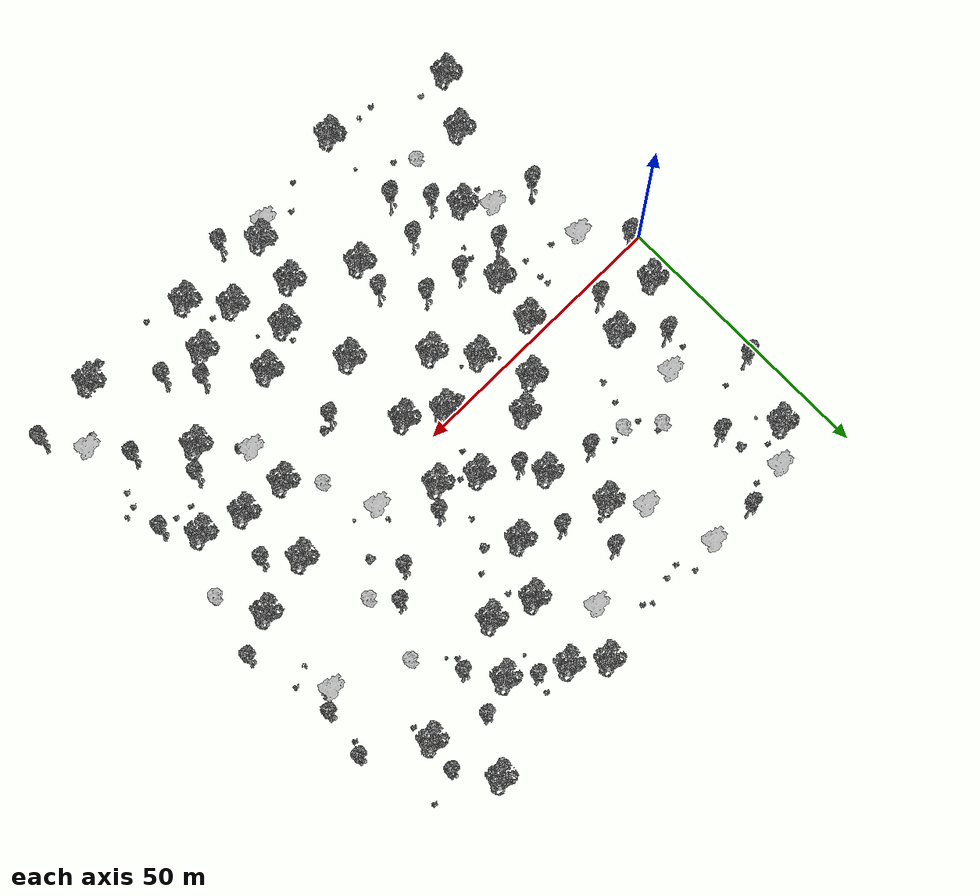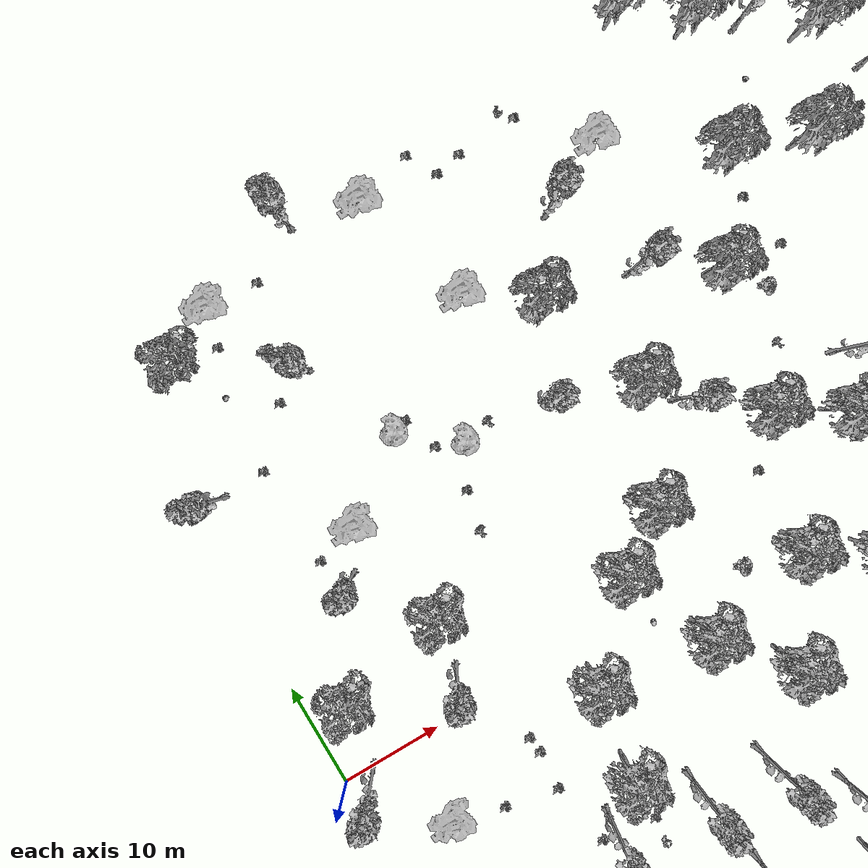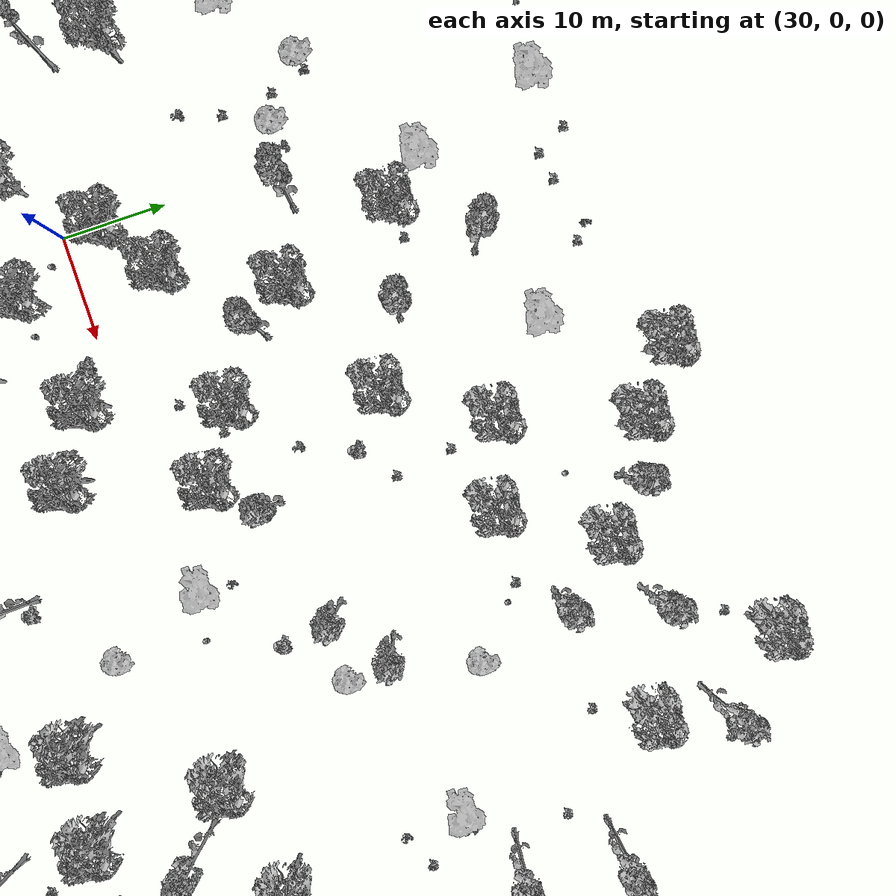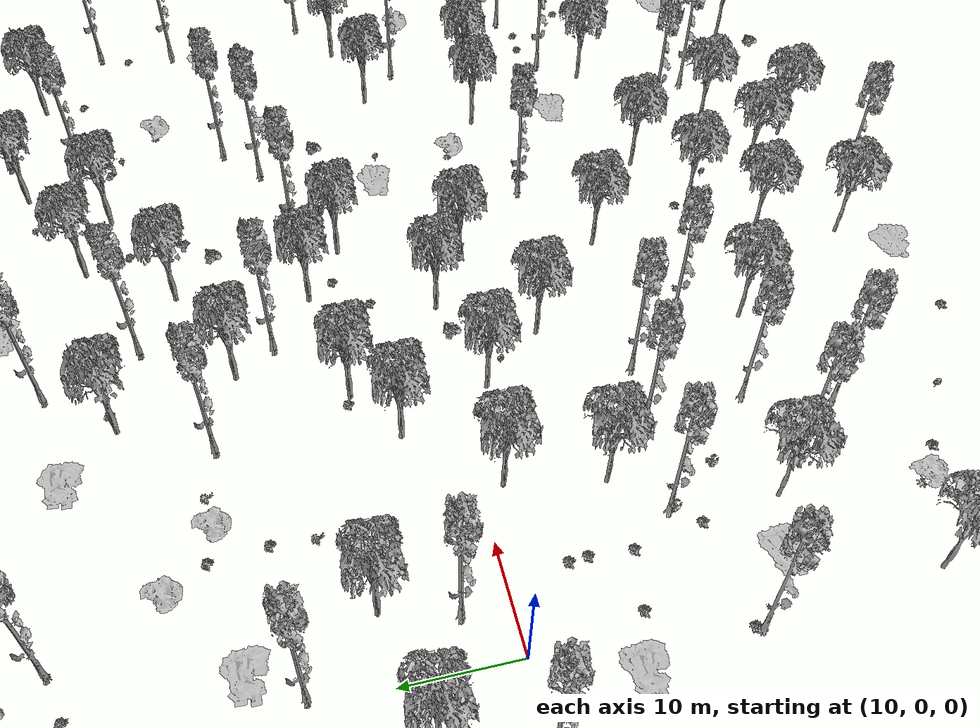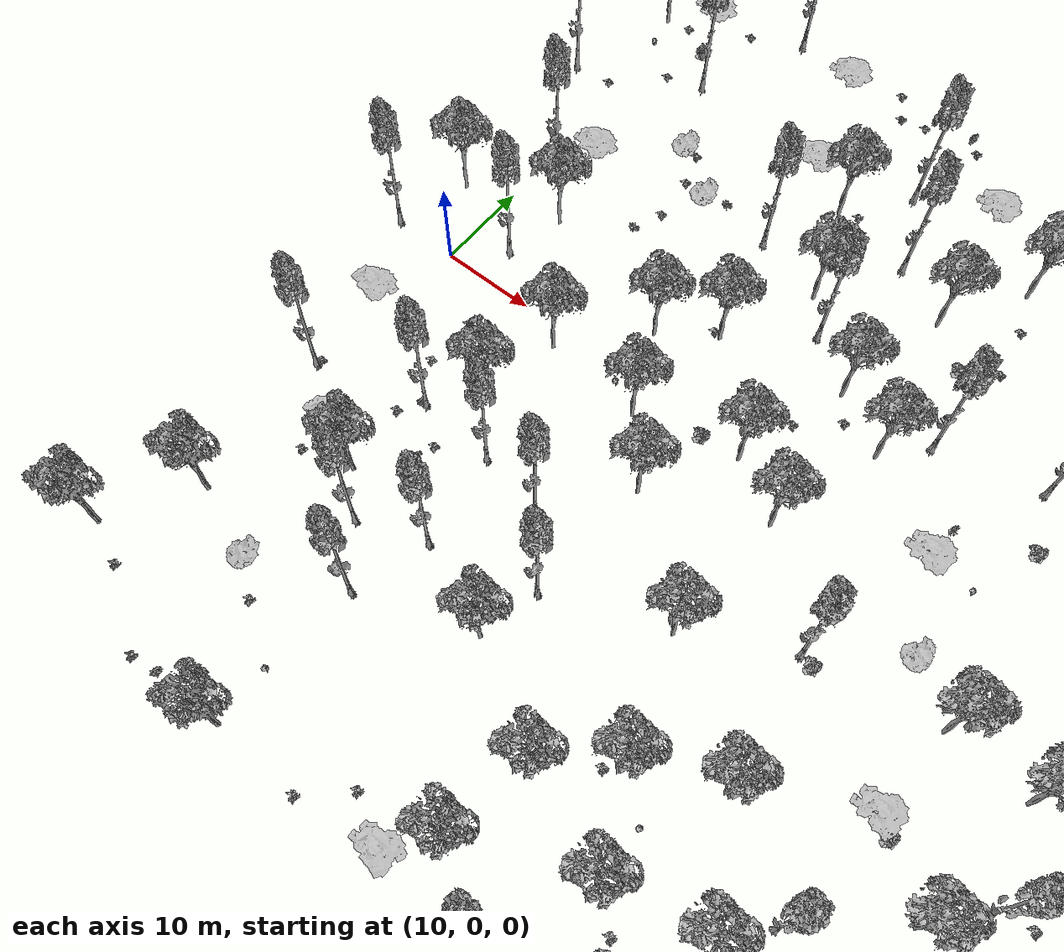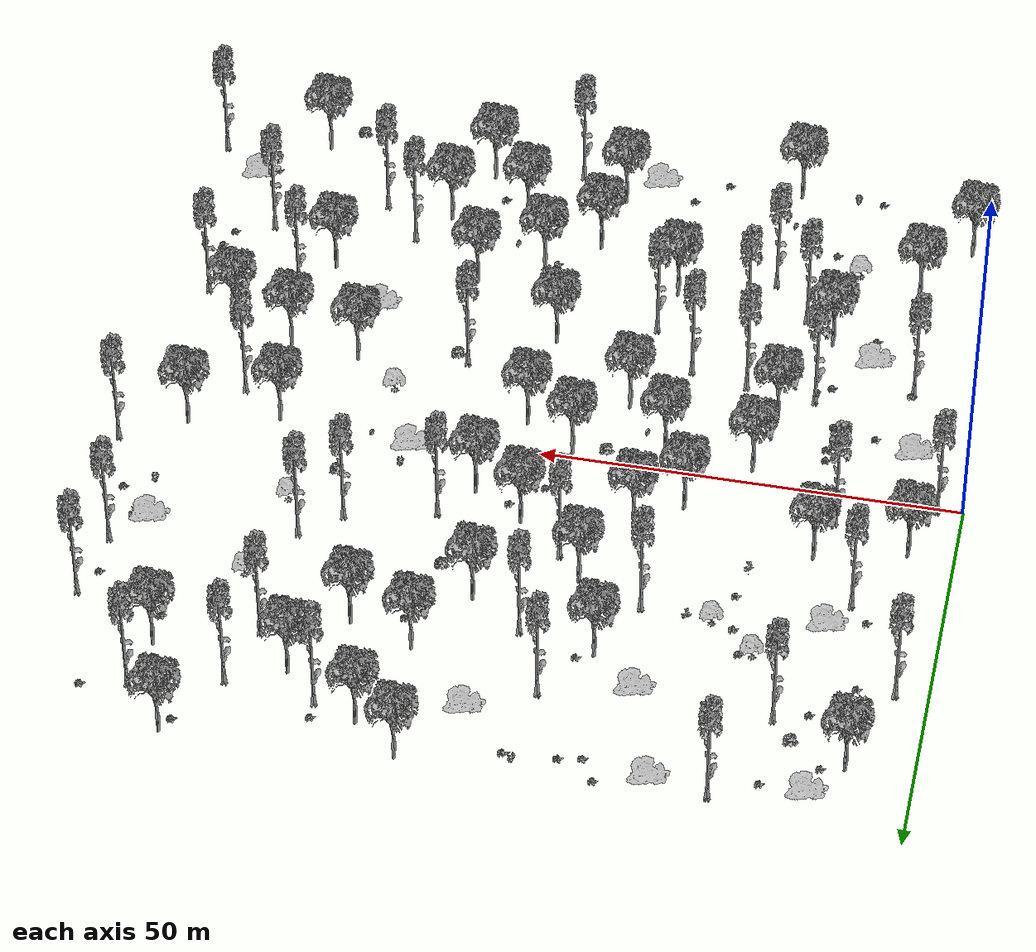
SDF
<sdf version="1.7">
 <world name="forest">
  <spherical_coordinates>
   <surface_model>EARTH_WGS84</surface_model>
   <latitude_deg>47.3977</latitude_deg>
   <longitude_deg>8.54559</longitude_deg>
   <elevation>0</elevation>
   <heading_deg>0</heading_deg>
  </spherical_coordinates>
  <physics name="default_physics" default="0" type="ode">
   <ode>
    <solver>
     <type>quick</type>
     <iters>10</iters>
     <sor>1.3</sor>
     <use_dynamic_moi_rescaling>0</use_dynamic_moi_rescaling>
    </solver>
    <constraints>
     <cfm>0</cfm>
     <erp>0.2</erp>
     <contact_max_correcting_vel>1000</contact_max_correcting_vel>
     <contact_surface_layer>0.001</contact_surface_layer>
    </constraints>
   </ode>
   <max_step_size>0.004</max_step_size>
   <real_time_factor>1</real_time_factor>
   <real_time_update_rate>250</real_time_update_rate>
  </physics>
  <plugin filename="gz-sim-scene-broadcaster-system" name="gz::sim::systems::SceneBroadcaster"/>
  <plugin filename="gz-sim-physics-system" name="gz::sim::systems::Physics"/>
  <plugin filename="gz-sim-user-commands-system" name="gz::sim::systems::UserCommands"/>
  <plugin filename="ignition-gazebo-sensors-system" name="gz::sim::systems::Sensors">
   <render_engine>ogre2</render_engine>
  </plugin>
  <plugin filename="gz-sim-imu-system" name="gz::sim::systems::Imu"/>
  <scene><shadows>0</shadows><ambient>0.4 0.4 0.4 1</ambient><background>0.7 0.7 0.7 1</background></scene>
  <light name="sun" type="directional">
   <pose>0 0 1000 0.4 0.2 0</pose>
   <diffuse>1 1 1 1</diffuse>
   <specular>0.0 0.0 0.0 1</specular>
   <direction>0.1 0.1 -0.9</direction>
   <attenuation>
    <range>20</range>
    <constant>0.5</constant>
    <linear>0.01</linear>
    <quadratic>0.001</quadratic>
   </attenuation>
   <cast_shadows>0</cast_shadows>
   <spot><inner_angle>0</inner_angle><outer_angle>0</outer_angle><falloff>0</falloff></spot>
  </light>
  <model name="controllable_camera">
   <pose>70 0 130 -1.5707 1.5707 0</pose>
   <static>true</static>
   <link name="base_link">
    <inertial><mass>0.1</mass><inertia><ixx>0.0001</ixx><iyy>0.0001</iyy><izz>0.0001</izz></inertia></inertial>
    <sensor name="gui_camera" type="rgbd_camera">
     <camera name="camera_front">
      <horizontal_fov>1.0472</horizontal_fov>
      <lens><intrinsics><fx>277.1</fx><fy>277.1</fy><cx>160.5</cx><cy>120.5</cy><s>0</s></intrinsics></lens>
      <distortion><k1>0.0</k1><k2>0.0</k2><k3>0.0</k3><p1>0.0</p1><p2>0.0</p2><center>0.5 0.5</center></distortion>
      <image><width>240</width><height>240</height><format>R8G8B8</format></image>
      <clip><near>0.01</near><far>300</far></clip>
      <depth_camera><clip><near>0.1</near><far>10</far></clip></depth_camera>
      <noise><type>gaussian</type><mean>0</mean><stddev>0.007</stddev></noise>
     </camera>
     <always_on>true</always_on>
     <update_rate>10</update_rate>
     <visualize>true</visualize>
    </sensor>
    <gravity>0</gravity>
   </link>
  </model>
  <gravity>0 0 -9.8066</gravity>
  <magnetic_field>6e-06 2.3e-05 -4.2e-05</magnetic_field>
  <atmosphere type="adiabatic"/>
  <model name="Tree 0">
   <static>1</static>
   <pose>29.54902566851168 -25.515385715936713 0 1.57079 -0 0</pose>
   <link name="link">
    <collision name="collision">
     <geometry><mesh><scale>3.5 5 3.5</scale><uri>model://tree_9/meshes/tree_9.obj</uri></mesh></geometry>
    </collision>
    <visual name="visual">
     <geometry><mesh><scale>3.5 5 3.5</scale><uri>model://tree_9/meshes/tree_9.obj</uri></mesh></geometry>
    </visual>
   </link>
  </model>
  <model name="Tree 1">
   <static>1</static>
   <pose>78.04902566851167 41.15128095072997 0 1.57079 -0 0</pose>
   <link name="link">
    <collision name="collision">
     <geometry><mesh><scale>3.5 5 3.5</scale><uri>model://tree_9/meshes/tree_9.obj</uri></mesh></geometry>
    </collision>
    <visual name="visual">
     <geometry><mesh><scale>3.5 5 3.5</scale><uri>model://tree_9/meshes/tree_9.obj</uri></mesh></geometry>
    </visual>
   </link>
  </model>
  <model name="Tree 2">
   <static>1</static>
   <pose>5.2990256685116774 7.817947617396648 0 1.57079 -0 0</pose>
   <link name="link">
    <collision name="collision">
     <geometry><mesh><scale>3.5 5 3.5</scale><uri>model://tree_2/meshes/tree_2.obj</uri></mesh></geometry>
    </collision>
    <visual name="visual">
     <geometry><mesh><scale>3.5 5 3.5</scale><uri>model://tree_2/meshes/tree_2.obj</uri></mesh></geometry>
    </visual>
   </link>
  </model>
  <model name="Tree 3">
   <static>1</static>
   <pose>53.799025668511675 -47.737607938158924 0 1.57079 -0 0</pose>
   <link name="link">
    <collision name="collision">
     <geometry><mesh><scale>3.5 5 3.5</scale><uri>model://tree_9/meshes/tree_9.obj</uri></mesh></geometry>
    </collision>
    <visual name="visual">
     <geometry><mesh><scale>3.5 5 3.5</scale><uri>model://tree_9/meshes/tree_9.obj</uri></mesh></geometry>
    </visual>
   </link>
  </model>
  <model name="Tree 4">
   <static>1</static>
   <pose>41.674025668511675 18.92905872850774 0 1.57079 -0 0</pose>
   <link name="link">
    <collision name="collision">
     <geometry><mesh><scale>3.5 5 3.5</scale><uri>model://tree_2/meshes/tree_2.obj</uri></mesh></geometry>
    </collision>
    <visual name="visual">
     <geometry><mesh><scale>3.5 5 3.5</scale><uri>model://tree_2/meshes/tree_2.obj</uri></mesh></geometry>
    </visual>
   </link>
  </model>
  <model name="Tree 5">
   <static>1</static>
   <pose>90.17402566851167 -14.404274604825588 0 1.57079 -0 0</pose>
   <link name="link">
    <collision name="collision">
     <geometry><mesh><scale>3.5 5 3.5</scale><uri>model://tree_2/meshes/tree_2.obj</uri></mesh></geometry>
    </collision>
    <visual name="visual">
     <geometry><mesh><scale>3.5 5 3.5</scale><uri>model://tree_2/meshes/tree_2.obj</uri></mesh></geometry>
    </visual>
   </link>
  </model>
  <model name="Tree 6">
   <static>1</static>
   <pose>17.42402566851168 -36.62649682704782 0 1.57079 -0 0</pose>
   <link name="link">
    <collision name="collision">
     <geometry><mesh><scale>4 2.5 4</scale><uri>model://tree_1/meshes/tree_1.obj</uri></mesh></geometry>
    </collision>
    <visual name="visual">
     <geometry><mesh><scale>4 2.5 4</scale><uri>model://tree_1/meshes/tree_1.obj</uri></mesh></geometry>
    </visual>
   </link>
  </model>
  <model name="Tree 7">
   <static>1</static>
   <pose>65.92402566851167 30.040169839618855 0 1.57079 -0 0</pose>
   <link name="link">
    <collision name="collision">
     <geometry><mesh><scale>3.5 5 3.5</scale><uri>model://tree_2/meshes/tree_2.obj</uri></mesh></geometry>
    </collision>
    <visual name="visual">
     <geometry><mesh><scale>3.5 5 3.5</scale><uri>model://tree_2/meshes/tree_2.obj</uri></mesh></geometry>
    </visual>
   </link>
  </model>
  <model name="Tree 8">
   <static>1</static>
   <pose>35.611525668511675 -3.2931634937144807 0 1.57079 -0 0</pose>
   <link name="link">
    <collision name="collision">
     <geometry><mesh><scale>3.5 5 3.5</scale><uri>model://tree_2/meshes/tree_2.obj</uri></mesh></geometry>
    </collision>
    <visual name="visual">
     <geometry><mesh><scale>3.5 5 3.5</scale><uri>model://tree_2/meshes/tree_2.obj</uri></mesh></geometry>
    </visual>
   </link>
  </model>
  <model name="Tree 9">
   <static>1</static>
   <pose>84.11152566851167 -21.811682012232996 0 1.57079 -0 0</pose>
   <link name="link">
    <collision name="collision">
     <geometry><mesh><scale>3.5 5 3.5</scale><uri>model://tree_9/meshes/tree_9.obj</uri></mesh></geometry>
    </collision>
    <visual name="visual">
     <geometry><mesh><scale>3.5 5 3.5</scale><uri>model://tree_9/meshes/tree_9.obj</uri></mesh></geometry>
    </visual>
   </link>
  </model>
  <model name="Tree 10">
   <static>1</static>
   <pose>11.361525668511678 44.85498465443368 0 1.57079 -0 0</pose>
   <link name="link">
    <collision name="collision">
     <geometry><mesh><scale>3 2 3</scale><uri>model://tree_3/meshes/tree_3.obj</uri></mesh></geometry>
    </collision>
    <visual name="visual">
     <geometry><mesh><scale>3 2 3</scale><uri>model://tree_3/meshes/tree_3.obj</uri></mesh></geometry>
    </visual>
   </link>
  </model>
  <model name="Tree 11">
   <static>1</static>
   <pose>59.861525668511675 11.521651321100343 0 1.57079 -0 0</pose>
   <link name="link">
    <collision name="collision">
     <geometry><mesh><scale>3.5 5 3.5</scale><uri>model://tree_9/meshes/tree_9.obj</uri></mesh></geometry>
    </collision>
    <visual name="visual">
     <geometry><mesh><scale>3.5 5 3.5</scale><uri>model://tree_9/meshes/tree_9.obj</uri></mesh></geometry>
    </visual>
   </link>
  </model>
  <model name="Tree 12">
   <static>1</static>
   <pose>47.736525668511675 -44.03390423445522 0 1.57079 -0 0</pose>
   <link name="link">
    <collision name="collision">
     <geometry><mesh><scale>3.5 5 3.5</scale><uri>model://tree_2/meshes/tree_2.obj</uri></mesh></geometry>
    </collision>
    <visual name="visual">
     <geometry><mesh><scale>3.5 5 3.5</scale><uri>model://tree_2/meshes/tree_2.obj</uri></mesh></geometry>
    </visual>
   </link>
  </model>
  <model name="Tree 13">
   <static>1</static>
   <pose>96.23652566851167 22.632762432211464 0 1.57079 -0 0</pose>
   <link name="link">
    <collision name="collision">
     <geometry><mesh><scale>3.5 5 3.5</scale><uri>model://tree_9/meshes/tree_9.obj</uri></mesh></geometry>
    </collision>
    <visual name="visual">
     <geometry><mesh><scale>3.5 5 3.5</scale><uri>model://tree_9/meshes/tree_9.obj</uri></mesh></geometry>
    </visual>
   </link>
  </model>
  <model name="Tree 14">
   <static>1</static>
   <pose>23.48652566851168 -10.700570901121885 0 1.57079 -0 0</pose>
   <link name="link">
    <collision name="collision">
     <geometry><mesh><scale>3.5 5 3.5</scale><uri>model://tree_2/meshes/tree_2.obj</uri></mesh></geometry>
    </collision>
    <visual name="visual">
     <geometry><mesh><scale>3.5 5 3.5</scale><uri>model://tree_2/meshes/tree_2.obj</uri></mesh></geometry>
    </visual>
   </link>
  </model>
  <model name="Tree 15">
   <static>1</static>
   <pose>71.98652566851167 -32.92279312334412 0 1.57079 -0 0</pose>
   <link name="link">
    <collision name="collision">
     <geometry><mesh><scale>3.5 5 3.5</scale><uri>model://tree_9/meshes/tree_9.obj</uri></mesh></geometry>
    </collision>
    <visual name="visual">
     <geometry><mesh><scale>3.5 5 3.5</scale><uri>model://tree_9/meshes/tree_9.obj</uri></mesh></geometry>
    </visual>
   </link>
  </model>
  <model name="Tree 16">
   <static>1</static>
   <pose>32.580275668511675 33.74387354332255 0 1.57079 -0 0</pose>
   <link name="link">
    <collision name="collision">
     <geometry><mesh><scale>3 2 3</scale><uri>model://tree_3/meshes/tree_3.obj</uri></mesh></geometry>
    </collision>
    <visual name="visual">
     <geometry><mesh><scale>3 2 3</scale><uri>model://tree_3/meshes/tree_3.obj</uri></mesh></geometry>
    </visual>
   </link>
  </model>
  <model name="Tree 17">
   <static>1</static>
   <pose>81.08027566851167 0.4105402099892288 0 1.57079 -0 0</pose>
   <link name="link">
    <collision name="collision">
     <geometry><mesh><scale>3.5 5 3.5</scale><uri>model://tree_2/meshes/tree_2.obj</uri></mesh></geometry>
    </collision>
    <visual name="visual">
     <geometry><mesh><scale>3.5 5 3.5</scale><uri>model://tree_2/meshes/tree_2.obj</uri></mesh></geometry>
    </visual>
   </link>
  </model>
  <model name="Tree 18">
   <static>1</static>
   <pose>8.330275668511678 -18.107978308529294 0 1.57079 -0 0</pose>
   <link name="link">
    <collision name="collision">
     <geometry><mesh><scale>3.5 5 3.5</scale><uri>model://tree_9/meshes/tree_9.obj</uri></mesh></geometry>
    </collision>
    <visual name="visual">
     <geometry><mesh><scale>3.5 5 3.5</scale><uri>model://tree_9/meshes/tree_9.obj</uri></mesh></geometry>
    </visual>
   </link>
  </model>
  <model name="Tree 19">
   <static>1</static>
   <pose>56.830275668511675 48.558688358137374 0 1.57079 -0 0</pose>
   <link name="link">
    <collision name="collision">
     <geometry><mesh><scale>3.5 5 3.5</scale><uri>model://tree_2/meshes/tree_2.obj</uri></mesh></geometry>
    </collision>
    <visual name="visual">
     <geometry><mesh><scale>3.5 5 3.5</scale><uri>model://tree_2/meshes/tree_2.obj</uri></mesh></geometry>
    </visual>
   </link>
  </model>
  <model name="Tree 20">
   <static>1</static>
   <pose>44.705275668511675 15.225355024804045 0 1.57079 -0 0</pose>
   <link name="link">
    <collision name="collision">
     <geometry><mesh><scale>3.5 5 3.5</scale><uri>model://tree_9/meshes/tree_9.obj</uri></mesh></geometry>
    </collision>
    <visual name="visual">
     <geometry><mesh><scale>3.5 5 3.5</scale><uri>model://tree_9/meshes/tree_9.obj</uri></mesh></geometry>
    </visual>
   </link>
  </model>
  <model name="Tree 21">
   <static>1</static>
   <pose>93.20527566851167 -40.33020053075151 0 1.57079 -0 0</pose>
   <link name="link">
    <collision name="collision">
     <geometry><mesh><scale>3 2 3</scale><uri>model://tree_3/meshes/tree_3.obj</uri></mesh></geometry>
    </collision>
    <visual name="visual">
     <geometry><mesh><scale>3 2 3</scale><uri>model://tree_3/meshes/tree_3.obj</uri></mesh></geometry>
    </visual>
   </link>
  </model>
  <model name="Tree 22">
   <static>1</static>
   <pose>20.45527566851168 26.33646613591516 0 1.57079 -0 0</pose>
   <link name="link">
    <collision name="collision">
     <geometry><mesh><scale>4 2.5 4</scale><uri>model://tree_1/meshes/tree_1.obj</uri></mesh></geometry>
    </collision>
    <visual name="visual">
     <geometry><mesh><scale>4 2.5 4</scale><uri>model://tree_1/meshes/tree_1.obj</uri></mesh></geometry>
    </visual>
   </link>
  </model>
  <model name="Tree 23">
   <static>1</static>
   <pose>68.95527566851167 -6.996867197418183 0 1.57079 -0 0</pose>
   <link name="link">
    <collision name="collision">
     <geometry><mesh><scale>4 2.5 4</scale><uri>model://tree_1/meshes/tree_1.obj</uri></mesh></geometry>
    </collision>
    <visual name="visual">
     <geometry><mesh><scale>4 2.5 4</scale><uri>model://tree_1/meshes/tree_1.obj</uri></mesh></geometry>
    </visual>
   </link>
  </model>
  <model name="Tree 24">
   <static>1</static>
   <pose>38.642775668511675 -29.21908941964042 0 1.57079 -0 0</pose>
   <link name="link">
    <collision name="collision">
     <geometry><mesh><scale>3.5 5 3.5</scale><uri>model://tree_2/meshes/tree_2.obj</uri></mesh></geometry>
    </collision>
    <visual name="visual">
     <geometry><mesh><scale>3.5 5 3.5</scale><uri>model://tree_2/meshes/tree_2.obj</uri></mesh></geometry>
    </visual>
   </link>
  </model>
  <model name="Tree 25">
   <static>1</static>
   <pose>87.14277566851167 37.44757724702626 0 1.57079 -0 0</pose>
   <link name="link">
    <collision name="collision">
     <geometry><mesh><scale>3.5 5 3.5</scale><uri>model://tree_2/meshes/tree_2.obj</uri></mesh></geometry>
    </collision>
    <visual name="visual">
     <geometry><mesh><scale>3.5 5 3.5</scale><uri>model://tree_2/meshes/tree_2.obj</uri></mesh></geometry>
    </visual>
   </link>
  </model>
  <model name="Tree 26">
   <static>1</static>
   <pose>14.392775668511678 4.114243913692931 0 1.57079 -0 0</pose>
   <link name="link">
    <collision name="collision">
     <geometry><mesh><scale>3.5 5 3.5</scale><uri>model://tree_9/meshes/tree_9.obj</uri></mesh></geometry>
    </collision>
    <visual name="visual">
     <geometry><mesh><scale>3.5 5 3.5</scale><uri>model://tree_9/meshes/tree_9.obj</uri></mesh></geometry>
    </visual>
   </link>
  </model>
  <model name="Tree 27">
   <static>1</static>
   <pose>62.892775668511675 -26.749953617171283 0 1.57079 -0 0</pose>
   <link name="link">
    <collision name="collision">
     <geometry><mesh><scale>3.5 5 3.5</scale><uri>model://tree_2/meshes/tree_2.obj</uri></mesh></geometry>
    </collision>
    <visual name="visual">
     <geometry><mesh><scale>3.5 5 3.5</scale><uri>model://tree_2/meshes/tree_2.obj</uri></mesh></geometry>
    </visual>
   </link>
  </model>
  <model name="Tree 28">
   <static>1</static>
   <pose>50.767775668511675 39.9167130494954 0 1.57079 -0 0</pose>
   <link name="link">
    <collision name="collision">
     <geometry><mesh><scale>3 2 3</scale><uri>model://tree_3/meshes/tree_3.obj</uri></mesh></geometry>
    </collision>
    <visual name="visual">
     <geometry><mesh><scale>3 2 3</scale><uri>model://tree_3/meshes/tree_3.obj</uri></mesh></geometry>
    </visual>
   </link>
  </model>
  <model name="Tree 29">
   <static>1</static>
   <pose>99.26777566851167 6.583379716162071 0 1.57079 -0 0</pose>
   <link name="link">
    <collision name="collision">
     <geometry><mesh><scale>3.5 5 3.5</scale><uri>model://tree_9/meshes/tree_9.obj</uri></mesh></geometry>
    </collision>
    <visual name="visual">
     <geometry><mesh><scale>3.5 5 3.5</scale><uri>model://tree_9/meshes/tree_9.obj</uri></mesh></geometry>
    </visual>
   </link>
  </model>
  <model name="Tree 30">
   <static>1</static>
   <pose>26.51777566851168 -48.97217583939349 0 1.57079 -0 0</pose>
   <link name="link">
    <collision name="collision">
     <geometry><mesh><scale>3.5 5 3.5</scale><uri>model://tree_2/meshes/tree_2.obj</uri></mesh></geometry>
    </collision>
    <visual name="visual">
     <geometry><mesh><scale>3.5 5 3.5</scale><uri>model://tree_2/meshes/tree_2.obj</uri></mesh></geometry>
    </visual>
   </link>
  </model>
  <model name="Tree 31">
   <static>1</static>
   <pose>75.01777566851167 17.694490827273185 0 1.57079 -0 0</pose>
   <link name="link">
    <collision name="collision">
     <geometry><mesh><scale>3.5 5 3.5</scale><uri>model://tree_9/meshes/tree_9.obj</uri></mesh></geometry>
    </collision>
    <visual name="visual">
     <geometry><mesh><scale>3.5 5 3.5</scale><uri>model://tree_9/meshes/tree_9.obj</uri></mesh></geometry>
    </visual>
   </link>
  </model>
  <model name="Tree 32">
   <static>1</static>
   <pose>28.03340066851168 -15.638842506060158 0 1.57079 -0 0</pose>
   <link name="link">
    <collision name="collision">
     <geometry><mesh><scale>3.5 5 3.5</scale><uri>model://tree_9/meshes/tree_9.obj</uri></mesh></geometry>
    </collision>
    <visual name="visual">
     <geometry><mesh><scale>3.5 5 3.5</scale><uri>model://tree_9/meshes/tree_9.obj</uri></mesh></geometry>
    </visual>
   </link>
  </model>
  <model name="Tree 33">
   <static>1</static>
   <pose>76.53340066851167 -37.86106472828238 0 1.57079 -0 0</pose>
   <link name="link">
    <collision name="collision">
     <geometry><mesh><scale>3.5 5 3.5</scale><uri>model://tree_9/meshes/tree_9.obj</uri></mesh></geometry>
    </collision>
    <visual name="visual">
     <geometry><mesh><scale>3.5 5 3.5</scale><uri>model://tree_9/meshes/tree_9.obj</uri></mesh></geometry>
    </visual>
   </link>
  </model>
  <model name="Tree 34">
   <static>1</static>
   <pose>3.7834006685116774 28.805601938384285 0 1.57079 -0 0</pose>
   <link name="link">
    <collision name="collision">
     <geometry><mesh><scale>3.5 5 3.5</scale><uri>model://tree_9/meshes/tree_9.obj</uri></mesh></geometry>
    </collision>
    <visual name="visual">
     <geometry><mesh><scale>3.5 5 3.5</scale><uri>model://tree_9/meshes/tree_9.obj</uri></mesh></geometry>
    </visual>
   </link>
  </model>
  <model name="Tree 35">
   <static>1</static>
   <pose>52.283400668511675 -4.5277313949490505 0 1.57079 -0 0</pose>
   <link name="link">
    <collision name="collision">
     <geometry><mesh><scale>3.5 5 3.5</scale><uri>model://tree_2/meshes/tree_2.obj</uri></mesh></geometry>
    </collision>
    <visual name="visual">
     <geometry><mesh><scale>3.5 5 3.5</scale><uri>model://tree_2/meshes/tree_2.obj</uri></mesh></geometry>
    </visual>
   </link>
  </model>
  <model name="Tree 36">
   <static>1</static>
   <pose>40.158400668511675 -23.046249913467566 0 1.57079 -0 0</pose>
   <link name="link">
    <collision name="collision">
     <geometry><mesh><scale>3.5 5 3.5</scale><uri>model://tree_9/meshes/tree_9.obj</uri></mesh></geometry>
    </collision>
    <visual name="visual">
     <geometry><mesh><scale>3.5 5 3.5</scale><uri>model://tree_9/meshes/tree_9.obj</uri></mesh></geometry>
    </visual>
   </link>
  </model>
  <model name="Tree 37">
   <static>1</static>
   <pose>88.65840066851167 43.620416753199095 0 1.57079 -0 0</pose>
   <link name="link">
    <collision name="collision">
     <geometry><mesh><scale>3.5 5 3.5</scale><uri>model://tree_9/meshes/tree_9.obj</uri></mesh></geometry>
    </collision>
    <visual name="visual">
     <geometry><mesh><scale>3.5 5 3.5</scale><uri>model://tree_9/meshes/tree_9.obj</uri></mesh></geometry>
    </visual>
   </link>
  </model>
  <model name="Tree 38">
   <static>1</static>
   <pose>15.908400668511678 10.287083419865773 0 1.57079 -0 0</pose>
   <link name="link">
    <collision name="collision">
     <geometry><mesh><scale>3.5 5 3.5</scale><uri>model://tree_2/meshes/tree_2.obj</uri></mesh></geometry>
    </collision>
    <visual name="visual">
     <geometry><mesh><scale>3.5 5 3.5</scale><uri>model://tree_2/meshes/tree_2.obj</uri></mesh></geometry>
    </visual>
   </link>
  </model>
  <model name="Tree 39">
   <static>1</static>
   <pose>64.40840066851167 -45.26847213568979 0 1.57079 -0 0</pose>
   <link name="link">
    <collision name="collision">
     <geometry><mesh><scale>3.5 5 3.5</scale><uri>model://tree_2/meshes/tree_2.obj</uri></mesh></geometry>
    </collision>
    <visual name="visual">
     <geometry><mesh><scale>3.5 5 3.5</scale><uri>model://tree_2/meshes/tree_2.obj</uri></mesh></geometry>
    </visual>
   </link>
  </model>
  <model name="Tree 40">
   <static>1</static>
   <pose>34.095900668511675 21.398194530976895 0 1.57079 -0 0</pose>
   <link name="link">
    <collision name="collision">
     <geometry><mesh><scale>3.5 5 3.5</scale><uri>model://tree_9/meshes/tree_9.obj</uri></mesh></geometry>
    </collision>
    <visual name="visual">
     <geometry><mesh><scale>3.5 5 3.5</scale><uri>model://tree_9/meshes/tree_9.obj</uri></mesh></geometry>
    </visual>
   </link>
  </model>
  <model name="Tree 41">
   <static>1</static>
   <pose>82.59590066851167 -11.935138802356455 0 1.57079 -0 0</pose>
   <link name="link">
    <collision name="collision">
     <geometry><mesh><scale>3.5 5 3.5</scale><uri>model://tree_2/meshes/tree_2.obj</uri></mesh></geometry>
    </collision>
    <visual name="visual">
     <geometry><mesh><scale>3.5 5 3.5</scale><uri>model://tree_2/meshes/tree_2.obj</uri></mesh></geometry>
    </visual>
   </link>
  </model>
  <model name="Tree 42">
   <static>1</static>
   <pose>9.845900668511678 -34.15736102457869 0 1.57079 -0 0</pose>
   <link name="link">
    <collision name="collision">
     <geometry><mesh><scale>3.5 5 3.5</scale><uri>model://tree_2/meshes/tree_2.obj</uri></mesh></geometry>
    </collision>
    <visual name="visual">
     <geometry><mesh><scale>3.5 5 3.5</scale><uri>model://tree_2/meshes/tree_2.obj</uri></mesh></geometry>
    </visual>
   </link>
  </model>
  <model name="Tree 43">
   <static>1</static>
   <pose>58.345900668511675 32.50930564208798 0 1.57079 -0 0</pose>
   <link name="link">
    <collision name="collision">
     <geometry><mesh><scale>3.5 5 3.5</scale><uri>model://tree_2/meshes/tree_2.obj</uri></mesh></geometry>
    </collision>
    <visual name="visual">
     <geometry><mesh><scale>3.5 5 3.5</scale><uri>model://tree_2/meshes/tree_2.obj</uri></mesh></geometry>
    </visual>
   </link>
  </model>
  <model name="Tree 44">
   <static>1</static>
   <pose>46.220900668511675 -0.824027691245341 0 1.57079 -0 0</pose>
   <link name="link">
    <collision name="collision">
     <geometry><mesh><scale>3.5 5 3.5</scale><uri>model://tree_2/meshes/tree_2.obj</uri></mesh></geometry>
    </collision>
    <visual name="visual">
     <geometry><mesh><scale>3.5 5 3.5</scale><uri>model://tree_2/meshes/tree_2.obj</uri></mesh></geometry>
    </visual>
   </link>
  </model>
  <model name="Tree 45">
   <static>1</static>
   <pose>94.72090066851167 -19.34254620976386 0 1.57079 -0 0</pose>
   <link name="link">
    <collision name="collision">
     <geometry><mesh><scale>3.5 5 3.5</scale><uri>model://tree_9/meshes/tree_9.obj</uri></mesh></geometry>
    </collision>
    <visual name="visual">
     <geometry><mesh><scale>3.5 5 3.5</scale><uri>model://tree_9/meshes/tree_9.obj</uri></mesh></geometry>
    </visual>
   </link>
  </model>
  <model name="Tree 46">
   <static>1</static>
   <pose>21.97090066851168 47.324120456902804 0 1.57079 -0 0</pose>
   <link name="link">
    <collision name="collision">
     <geometry><mesh><scale>3.5 5 3.5</scale><uri>model://tree_9/meshes/tree_9.obj</uri></mesh></geometry>
     <surface><friction><torsional>camera</torsional></friction></surface>
    </collision>
    <visual name="visual">
     <geometry><mesh><scale>3.5 5 3.5</scale><uri>model://tree_9/meshes/tree_9.obj</uri></mesh></geometry>
    </visual>
   </link>
  </model>
  <model name="Tree 47">
   <static>1</static>
   <pose>70.47090066851167 13.990787123569483 0 1.57079 -0 0</pose>
   <link name="link">
    <collision name="collision">
     <geometry><mesh><scale>3.5 5 3.5</scale><uri>model://tree_9/meshes/tree_9.obj</uri></mesh></geometry>
    </collision>
    <visual name="visual">
     <geometry><mesh><scale>3.5 5 3.5</scale><uri>model://tree_9/meshes/tree_9.obj</uri></mesh></geometry>
    </visual>
   </link>
  </model>
  <model name="Tree 49">
   <static>1</static>
   <pose>79.56465066851167 25.10189823468059 0 1.57079 -0 0</pose>
   <link name="link">
    <collision name="collision">
     <geometry><mesh><scale>4 2.5 4</scale><uri>model://tree_1/meshes/tree_1.obj</uri></mesh></geometry>
    </collision>
    <visual name="visual">
     <geometry><mesh><scale>4 2.5 4</scale><uri>model://tree_1/meshes/tree_1.obj</uri></mesh></geometry>
    </visual>
   </link>
  </model>
  <model name="Tree 50">
   <static>1</static>
   <pose>6.8146506685116774 -8.231435098652753 0 1.57079 -0 0</pose>
   <link name="link">
    <collision name="collision">
     <geometry><mesh><scale>3 2 3</scale><uri>model://tree_3/meshes/tree_3.obj</uri></mesh></geometry>
    </collision>
    <visual name="visual">
     <geometry><mesh><scale>3 2 3</scale><uri>model://tree_3/meshes/tree_3.obj</uri></mesh></geometry>
    </visual>
   </link>
  </model>
  <model name="Tree 51">
   <static>1</static>
   <pose>55.314650668511675 -30.453657320874985 0 1.57079 -0 0</pose>
   <link name="link">
    <collision name="collision">
     <geometry><mesh><scale>3.5 5 3.5</scale><uri>model://tree_2/meshes/tree_2.obj</uri></mesh></geometry>
    </collision>
    <visual name="visual">
     <geometry><mesh><scale>3.5 5 3.5</scale><uri>model://tree_2/meshes/tree_2.obj</uri></mesh></geometry>
    </visual>
   </link>
  </model>
  <model name="Tree 52">
   <static>1</static>
   <pose>43.189650668511675 36.21300934579169 0 1.57079 -0 0</pose>
   <link name="link">
    <collision name="collision">
     <geometry><mesh><scale>3.5 5 3.5</scale><uri>model://tree_9/meshes/tree_9.obj</uri></mesh></geometry>
    </collision>
    <visual name="visual">
     <geometry><mesh><scale>3.5 5 3.5</scale><uri>model://tree_9/meshes/tree_9.obj</uri></mesh></geometry>
    </visual>
   </link>
  </model>
  <model name="Tree 53">
   <static>1</static>
   <pose>91.68965066851167 2.8796760124583685 0 1.57079 -0 0</pose>
   <link name="link">
    <collision name="collision">
     <geometry><mesh><scale>3.5 5 3.5</scale><uri>model://tree_2/meshes/tree_2.obj</uri></mesh></geometry>
    </collision>
    <visual name="visual">
     <geometry><mesh><scale>3.5 5 3.5</scale><uri>model://tree_2/meshes/tree_2.obj</uri></mesh></geometry>
    </visual>
   </link>
  </model>
  <model name="Tree 54">
   <static>1</static>
   <pose>18.93965066851168 -24.280817814702132 0 1.57079 -0 0</pose>
   <link name="link">
    <collision name="collision">
     <geometry><mesh><scale>3.5 5 3.5</scale><uri>model://tree_2/meshes/tree_2.obj</uri></mesh></geometry>
    </collision>
    <visual name="visual">
     <geometry><mesh><scale>3.5 5 3.5</scale><uri>model://tree_2/meshes/tree_2.obj</uri></mesh></geometry>
    </visual>
   </link>
  </model>
  <model name="Tree 55">
   <static>1</static>
   <pose>67.43965066851167 42.38584885196454 0 1.57079 -0 0</pose>
   <link name="link">
    <collision name="collision">
     <geometry><mesh><scale>3.5 5 3.5</scale><uri>model://tree_9/meshes/tree_9.obj</uri></mesh></geometry>
    </collision>
    <visual name="visual">
     <geometry><mesh><scale>3.5 5 3.5</scale><uri>model://tree_9/meshes/tree_9.obj</uri></mesh></geometry>
    </visual>
   </link>
  </model>
  <model name="Tree 56">
   <static>1</static>
   <pose>37.127150668511675 9.05251551863121 0 1.57079 -0 0</pose>
   <link name="link">
    <collision name="collision">
     <geometry><mesh><scale>3.5 5 3.5</scale><uri>model://tree_2/meshes/tree_2.obj</uri></mesh></geometry>
    </collision>
    <visual name="visual">
     <geometry><mesh><scale>3.5 5 3.5</scale><uri>model://tree_2/meshes/tree_2.obj</uri></mesh></geometry>
    </visual>
   </link>
  </model>
  <model name="Tree 57">
   <static>1</static>
   <pose>85.62715066851167 -46.503040036924354 0 1.57079 -0 0</pose>
   <link name="link">
    <collision name="collision">
     <geometry><mesh><scale>3.5 5 3.5</scale><uri>model://tree_2/meshes/tree_2.obj</uri></mesh></geometry>
    </collision>
    <visual name="visual">
     <geometry><mesh><scale>3.5 5 3.5</scale><uri>model://tree_2/meshes/tree_2.obj</uri></mesh></geometry>
    </visual>
   </link>
  </model>
  <model name="Tree 58">
   <static>1</static>
   <pose>12.877150668511678 20.16362662974231 0 1.57079 -0 0</pose>
   <link name="link">
    <collision name="collision">
     <geometry><mesh><scale>3 2 3</scale><uri>model://tree_3/meshes/tree_3.obj</uri></mesh></geometry>
    </collision>
    <visual name="visual">
     <geometry><mesh><scale>3 2 3</scale><uri>model://tree_3/meshes/tree_3.obj</uri></mesh></geometry>
    </visual>
   </link>
  </model>
  <model name="Tree 59">
   <static>1</static>
   <pose>61.377150668511675 -13.169706703591025 0 1.57079 -0 0</pose>
   <link name="link">
    <collision name="collision">
     <geometry><mesh><scale>3.5 5 3.5</scale><uri>model://tree_9/meshes/tree_9.obj</uri></mesh></geometry>
    </collision>
    <visual name="visual">
     <geometry><mesh><scale>3.5 5 3.5</scale><uri>model://tree_9/meshes/tree_9.obj</uri></mesh></geometry>
    </visual>
   </link>
  </model>
  <model name="Tree 60">
   <static>1</static>
   <pose>49.252150668511675 -35.39192892581326 0 1.57079 -0 0</pose>
   <link name="link">
    <collision name="collision">
     <geometry><mesh><scale>3.5 5 3.5</scale><uri>model://tree_2/meshes/tree_2.obj</uri></mesh></geometry>
    </collision>
    <visual name="visual">
     <geometry><mesh><scale>3.5 5 3.5</scale><uri>model://tree_2/meshes/tree_2.obj</uri></mesh></geometry>
    </visual>
   </link>
  </model>
  <model name="Tree 61">
   <static>1</static>
   <pose>97.75215066851167 31.274737740853425 0 1.57079 -0 0</pose>
   <link name="link">
    <collision name="collision">
     <geometry><mesh><scale>3.5 5 3.5</scale><uri>model://tree_9/meshes/tree_9.obj</uri></mesh></geometry>
    </collision>
    <visual name="visual">
     <geometry><mesh><scale>3.5 5 3.5</scale><uri>model://tree_9/meshes/tree_9.obj</uri></mesh></geometry>
    </visual>
   </link>
  </model>
  <model name="Tree 62">
   <static>1</static>
   <pose>25.00215066851168 -2.058595592479911 0 1.57079 -0 0</pose>
   <link name="link">
    <collision name="collision">
     <geometry><mesh><scale>3.5 5 3.5</scale><uri>model://tree_2/meshes/tree_2.obj</uri></mesh></geometry>
    </collision>
    <visual name="visual">
     <geometry><mesh><scale>3.5 5 3.5</scale><uri>model://tree_2/meshes/tree_2.obj</uri></mesh></geometry>
    </visual>
   </link>
  </model>
  <model name="Tree 63">
   <static>1</static>
   <pose>73.50215066851167 -20.57711411099843 0 1.57079 -0 0</pose>
   <link name="link">
    <collision name="collision">
     <geometry><mesh><scale>3 2 3</scale><uri>model://tree_3/meshes/tree_3.obj</uri></mesh></geometry>
    </collision>
    <visual name="visual">
     <geometry><mesh><scale>3 2 3</scale><uri>model://tree_3/meshes/tree_3.obj</uri></mesh></geometry>
    </visual>
   </link>
  </model>
  <model name="Tree 64">
   <static>1</static>
   <pose>28.79121316851168 46.089552555668234 0 1.57079 -0 0</pose>
   <link name="link">
    <collision name="collision">
     <geometry><mesh><scale>3 2 3</scale><uri>model://tree_3/meshes/tree_3.obj</uri></mesh></geometry>
    </collision>
    <visual name="visual">
     <geometry><mesh><scale>3 2 3</scale><uri>model://tree_3/meshes/tree_3.obj</uri></mesh></geometry>
    </visual>
   </link>
  </model>
  <model name="Tree 65">
   <static>1</static>
   <pose>77.29121316851167 12.756219222334906 0 1.57079 -0 0</pose>
   <link name="link">
    <collision name="collision">
     <geometry><mesh><scale>4 2.5 4</scale><uri>model://tree_1/meshes/tree_1.obj</uri></mesh></geometry>
    </collision>
    <visual name="visual">
     <geometry><mesh><scale>4 2.5 4</scale><uri>model://tree_1/meshes/tree_1.obj</uri></mesh></geometry>
    </visual>
   </link>
  </model>
  <model name="Tree 66">
   <static>1</static>
   <pose>4.5412131685116774 -42.79933633322065 0 1.57079 -0 0</pose>
   <link name="link">
    <collision name="collision">
     <geometry><mesh><scale>3.5 5 3.5</scale><uri>model://tree_2/meshes/tree_2.obj</uri></mesh></geometry>
    </collision>
    <visual name="visual">
     <geometry><mesh><scale>3.5 5 3.5</scale><uri>model://tree_2/meshes/tree_2.obj</uri></mesh></geometry>
    </visual>
   </link>
  </model>
  <model name="Tree 67">
   <static>1</static>
   <pose>53.041213168511675 23.86733033344602 0 1.57079 -0 0</pose>
   <link name="link">
    <collision name="collision">
     <geometry><mesh><scale>3.5 5 3.5</scale><uri>model://tree_2/meshes/tree_2.obj</uri></mesh></geometry>
    </collision>
    <visual name="visual">
     <geometry><mesh><scale>3.5 5 3.5</scale><uri>model://tree_2/meshes/tree_2.obj</uri></mesh></geometry>
    </visual>
   </link>
  </model>
  <model name="Tree 68">
   <static>1</static>
   <pose>40.916213168511675 -9.466002999887316 0 1.57079 -0 0</pose>
   <link name="link">
    <collision name="collision">
     <geometry><mesh><scale>3.5 5 3.5</scale><uri>model://tree_2/meshes/tree_2.obj</uri></mesh></geometry>
    </collision>
    <visual name="visual">
     <geometry><mesh><scale>3.5 5 3.5</scale><uri>model://tree_2/meshes/tree_2.obj</uri></mesh></geometry>
    </visual>
   </link>
  </model>
  <model name="Tree 69">
   <static>1</static>
   <pose>89.41621316851167 -31.688225222109555 0 1.57079 -0 0</pose>
   <link name="link">
    <collision name="collision">
     <geometry><mesh><scale>3.5 5 3.5</scale><uri>model://tree_9/meshes/tree_9.obj</uri></mesh></geometry>
    </collision>
    <visual name="visual">
     <geometry><mesh><scale>3.5 5 3.5</scale><uri>model://tree_9/meshes/tree_9.obj</uri></mesh></geometry>
    </visual>
   </link>
  </model>
  <model name="Tree 70">
   <static>1</static>
   <pose>16.66621316851168 34.97844144455712 0 1.57079 -0 0</pose>
   <link name="link">
    <collision name="collision">
     <geometry><mesh><scale>3.5 5 3.5</scale><uri>model://tree_9/meshes/tree_9.obj</uri></mesh></geometry>
    </collision>
    <visual name="visual">
     <geometry><mesh><scale>3.5 5 3.5</scale><uri>model://tree_9/meshes/tree_9.obj</uri></mesh></geometry>
    </visual>
   </link>
  </model>
  <model name="Tree 71">
   <static>1</static>
   <pose>65.16621316851167 1.6451081112238057 0 1.57079 -0 0</pose>
   <link name="link">
    <collision name="collision">
     <geometry><mesh><scale>3 2 3</scale><uri>model://tree_3/meshes/tree_3.obj</uri></mesh></geometry>
    </collision>
    <visual name="visual">
     <geometry><mesh><scale>3 2 3</scale><uri>model://tree_3/meshes/tree_3.obj</uri></mesh></geometry>
    </visual>
   </link>
  </model>
  <model name="Tree 72">
   <static>1</static>
   <pose>34.853713168511675 -16.873410407294728 0 1.57079 -0 0</pose>
   <link name="link">
    <collision name="collision">
     <geometry><mesh><scale>3.5 5 3.5</scale><uri>model://tree_9/meshes/tree_9.obj</uri></mesh></geometry>
    </collision>
    <visual name="visual">
     <geometry><mesh><scale>3.5 5 3.5</scale><uri>model://tree_9/meshes/tree_9.obj</uri></mesh></geometry>
    </visual>
   </link>
  </model>
  <model name="Tree 73">
   <static>1</static>
   <pose>83.35371316851167 49.793256259371944 0 1.57079 -0 0</pose>
   <link name="link">
    <collision name="collision">
     <geometry><mesh><scale>3.5 5 3.5</scale><uri>model://tree_2/meshes/tree_2.obj</uri></mesh></geometry>
    </collision>
    <visual name="visual">
     <geometry><mesh><scale>3.5 5 3.5</scale><uri>model://tree_2/meshes/tree_2.obj</uri></mesh></geometry>
    </visual>
   </link>
  </model>
  <model name="Tree 74">
   <static>1</static>
   <pose>10.603713168511678 16.459922926038615 0 1.57079 -0 0</pose>
   <link name="link">
    <collision name="collision">
     <geometry><mesh><scale>3.5 5 3.5</scale><uri>model://tree_9/meshes/tree_9.obj</uri></mesh></geometry>
    </collision>
    <visual name="visual">
     <geometry><mesh><scale>3.5 5 3.5</scale><uri>model://tree_9/meshes/tree_9.obj</uri></mesh></geometry>
    </visual>
   </link>
  </model>
  <model name="Tree 75">
   <static>1</static>
   <pose>59.103713168511675 -39.09563262951695 0 1.57079 -0 0</pose>
   <link name="link">
    <collision name="collision">
     <geometry><mesh><scale>3.5 5 3.5</scale><uri>model://tree_2/meshes/tree_2.obj</uri></mesh></geometry>
    </collision>
    <visual name="visual">
     <geometry><mesh><scale>3.5 5 3.5</scale><uri>model://tree_2/meshes/tree_2.obj</uri></mesh></geometry>
    </visual>
   </link>
  </model>
  <model name="Tree 76">
   <static>1</static>
   <pose>46.978713168511675 27.571034037149715 0 1.57079 -0 0</pose>
   <link name="link">
    <collision name="collision">
     <geometry><mesh><scale>3.5 5 3.5</scale><uri>model://tree_9/meshes/tree_9.obj</uri></mesh></geometry>
    </collision>
    <visual name="visual">
     <geometry><mesh><scale>3.5 5 3.5</scale><uri>model://tree_9/meshes/tree_9.obj</uri></mesh></geometry>
    </visual>
   </link>
  </model>
  <model name="Tree 77">
   <static>1</static>
   <pose>95.47871316851167 -5.762299296183613 0 1.57079 -0 0</pose>
   <link name="link">
    <collision name="collision">
     <geometry><mesh><scale>4 2.5 4</scale><uri>model://tree_1/meshes/tree_1.obj</uri></mesh></geometry>
    </collision>
    <visual name="visual">
     <geometry><mesh><scale>4 2.5 4</scale><uri>model://tree_1/meshes/tree_1.obj</uri></mesh></geometry>
    </visual>
   </link>
  </model>
  <model name="Tree 78">
   <static>1</static>
   <pose>22.72871316851168 -27.98452151840585 0 1.57079 -0 0</pose>
   <link name="link">
    <collision name="collision">
     <geometry><mesh><scale>3.5 5 3.5</scale><uri>model://tree_9/meshes/tree_9.obj</uri></mesh></geometry>
    </collision>
    <visual name="visual">
     <geometry><mesh><scale>3.5 5 3.5</scale><uri>model://tree_9/meshes/tree_9.obj</uri></mesh></geometry>
    </visual>
   </link>
  </model>
  <model name="Tree 79">
   <static>1</static>
   <pose>71.22871316851167 38.68214514826083 0 1.57079 -0 0</pose>
   <link name="link">
    <collision name="collision">
     <geometry><mesh><scale>3.5 5 3.5</scale><uri>model://tree_2/meshes/tree_2.obj</uri></mesh></geometry>
    </collision>
    <visual name="visual">
     <geometry><mesh><scale>3.5 5 3.5</scale><uri>model://tree_2/meshes/tree_2.obj</uri></mesh></geometry>
    </visual>
   </link>
  </model>
  <model name="Tree 80">
   <static>1</static>
   <pose>31.82246316851168 5.348811814927501 0 1.57079 -0 0</pose>
   <link name="link">
    <collision name="collision">
     <geometry><mesh><scale>3.5 5 3.5</scale><uri>model://tree_2/meshes/tree_2.obj</uri></mesh></geometry>
    </collision>
    <visual name="visual">
     <geometry><mesh><scale>3.5 5 3.5</scale><uri>model://tree_2/meshes/tree_2.obj</uri></mesh></geometry>
    </visual>
   </link>
  </model>
  <model name="Tree 81">
   <static>1</static>
   <pose>80.32246316851167 -25.926908349681568 0 1.57079 -0 0</pose>
   <link name="link">
    <collision name="collision">
     <geometry><mesh><scale>3.5 5 3.5</scale><uri>model://tree_2/meshes/tree_2.obj</uri></mesh></geometry>
    </collision>
    <visual name="visual">
     <geometry><mesh><scale>3.5 5 3.5</scale><uri>model://tree_2/meshes/tree_2.obj</uri></mesh></geometry>
    </visual>
   </link>
  </model>
  <model name="Tree 82">
   <static>1</static>
   <pose>7.5724631685116774 40.73975831698512 0 1.57079 -0 0</pose>
   <link name="link">
    <collision name="collision">
     <geometry><mesh><scale>3.5 5 3.5</scale><uri>model://tree_2/meshes/tree_2.obj</uri></mesh></geometry>
    </collision>
    <visual name="visual">
     <geometry><mesh><scale>3.5 5 3.5</scale><uri>model://tree_2/meshes/tree_2.obj</uri></mesh></geometry>
    </visual>
   </link>
  </model>
  <model name="Tree 83">
   <static>1</static>
   <pose>56.072463168511675 7.406424983651796 0 1.57079 -0 0</pose>
   <link name="link">
    <collision name="collision">
     <geometry><mesh><scale>3.5 5 3.5</scale><uri>model://tree_2/meshes/tree_2.obj</uri></mesh></geometry>
    </collision>
    <visual name="visual">
     <geometry><mesh><scale>3.5 5 3.5</scale><uri>model://tree_2/meshes/tree_2.obj</uri></mesh></geometry>
    </visual>
   </link>
  </model>
  <model name="Tree 84">
   <static>1</static>
   <pose>43.947463168511675 -48.14913057190378 0 1.57079 -0 0</pose>
   <link name="link">
    <collision name="collision">
     <geometry><mesh><scale>3 2 3</scale><uri>model://tree_3/meshes/tree_3.obj</uri></mesh></geometry>
    </collision>
    <visual name="visual">
     <geometry><mesh><scale>3 2 3</scale><uri>model://tree_3/meshes/tree_3.obj</uri></mesh></geometry>
    </visual>
   </link>
  </model>
  <model name="Tree 85">
   <static>1</static>
   <pose>92.44746316851167 18.51753609476289 0 1.57079 -0 0</pose>
   <link name="link">
    <collision name="collision">
     <geometry><mesh><scale>3 2 3</scale><uri>model://tree_3/meshes/tree_3.obj</uri></mesh></geometry>
    </collision>
    <visual name="visual">
     <geometry><mesh><scale>3 2 3</scale><uri>model://tree_3/meshes/tree_3.obj</uri></mesh></geometry>
    </visual>
   </link>
  </model>
  <model name="Tree 86">
   <static>1</static>
   <pose>19.69746316851168 -14.815797238570447 0 1.57079 -0 0</pose>
   <link name="link">
    <collision name="collision">
     <geometry><mesh><scale>3.5 5 3.5</scale><uri>model://tree_9/meshes/tree_9.obj</uri></mesh></geometry>
    </collision>
    <visual name="visual">
     <geometry><mesh><scale>3.5 5 3.5</scale><uri>model://tree_9/meshes/tree_9.obj</uri></mesh></geometry>
    </visual>
   </link>
  </model>
  <model name="Tree 87">
   <static>1</static>
   <pose>68.19746316851167 -37.03801946079268 0 1.57079 -0 0</pose>
   <link name="link">
    <collision name="collision">
     <geometry><mesh><scale>3.5 5 3.5</scale><uri>model://tree_2/meshes/tree_2.obj</uri></mesh></geometry>
    </collision>
    <visual name="visual">
     <geometry><mesh><scale>3.5 5 3.5</scale><uri>model://tree_2/meshes/tree_2.obj</uri></mesh></geometry>
    </visual>
   </link>
  </model>
  <model name="Tree 88">
   <static>1</static>
   <pose>37.884963168511675 29.628647205874003 0 1.57079 -0 0</pose>
   <link name="link">
    <collision name="collision">
     <geometry><mesh><scale>3.5 5 3.5</scale><uri>model://tree_2/meshes/tree_2.obj</uri></mesh></geometry>
    </collision>
    <visual name="visual">
     <geometry><mesh><scale>3.5 5 3.5</scale><uri>model://tree_2/meshes/tree_2.obj</uri></mesh></geometry>
    </visual>
   </link>
  </model>
  <model name="Tree 89">
   <static>1</static>
   <pose>86.38496316851167 -3.7046861274593397 0 1.57079 -0 0</pose>
   <link name="link">
    <collision name="collision">
     <geometry><mesh><scale>3.5 5 3.5</scale><uri>model://tree_9/meshes/tree_9.obj</uri></mesh></geometry>
    </collision>
    <visual name="visual">
     <geometry><mesh><scale>3.5 5 3.5</scale><uri>model://tree_9/meshes/tree_9.obj</uri></mesh></geometry>
    </visual>
   </link>
  </model>
  <model name="Tree 90">
   <static>1</static>
   <pose>13.634963168511678 -22.223204645977855 0 1.57079 -0 0</pose>
   <link name="link">
    <collision name="collision">
     <geometry><mesh><scale>3 2 3</scale><uri>model://tree_3/meshes/tree_3.obj</uri></mesh></geometry>
    </collision>
    <visual name="visual">
     <geometry><mesh><scale>3 2 3</scale><uri>model://tree_3/meshes/tree_3.obj</uri></mesh></geometry>
    </visual>
   </link>
  </model>
  <model name="Tree 91">
   <static>1</static>
   <pose>62.134963168511675 44.44346202068881 0 1.57079 -0 0</pose>
   <link name="link">
    <collision name="collision">
     <geometry><mesh><scale>3.5 5 3.5</scale><uri>model://tree_2/meshes/tree_2.obj</uri></mesh></geometry>
    </collision>
    <visual name="visual">
     <geometry><mesh><scale>3.5 5 3.5</scale><uri>model://tree_2/meshes/tree_2.obj</uri></mesh></geometry>
    </visual>
   </link>
  </model>
  <model name="Tree 92">
   <static>1</static>
   <pose>50.009963168511675 11.110128687355491 0 1.57079 -0 0</pose>
   <link name="link">
    <collision name="collision">
     <geometry><mesh><scale>3.5 5 3.5</scale><uri>model://tree_2/meshes/tree_2.obj</uri></mesh></geometry>
    </collision>
    <visual name="visual">
     <geometry><mesh><scale>3.5 5 3.5</scale><uri>model://tree_2/meshes/tree_2.obj</uri></mesh></geometry>
    </visual>
   </link>
  </model>
  <model name="Tree 93">
   <static>1</static>
   <pose>98.50996316851167 -44.44542686820007 0 1.57079 -0 0</pose>
   <link name="link">
    <collision name="collision">
     <geometry><mesh><scale>3.5 5 3.5</scale><uri>model://tree_9/meshes/tree_9.obj</uri></mesh></geometry>
    </collision>
    <visual name="visual">
     <geometry><mesh><scale>3.5 5 3.5</scale><uri>model://tree_9/meshes/tree_9.obj</uri></mesh></geometry>
    </visual>
   </link>
  </model>
  <model name="Tree 94">
   <static>1</static>
   <pose>25.75996316851168 22.221239798466613 0 1.57079 -0 0</pose>
   <link name="link">
    <collision name="collision">
     <geometry><mesh><scale>4 2.5 4</scale><uri>model://tree_1/meshes/tree_1.obj</uri></mesh></geometry>
    </collision>
    <visual name="visual">
     <geometry><mesh><scale>4 2.5 4</scale><uri>model://tree_1/meshes/tree_1.obj</uri></mesh></geometry>
    </visual>
   </link>
  </model>
  <model name="Tree 95">
   <static>1</static>
   <pose>74.25996316851167 -11.112093534866744 0 1.57079 -0 0</pose>
   <link name="link">
    <collision name="collision">
     <geometry><mesh><scale>3.5 5 3.5</scale><uri>model://tree_2/meshes/tree_2.obj</uri></mesh></geometry>
    </collision>
    <visual name="visual">
     <geometry><mesh><scale>3.5 5 3.5</scale><uri>model://tree_2/meshes/tree_2.obj</uri></mesh></geometry>
    </visual>
   </link>
  </model>
  <model name="Tree 96">
   <static>1</static>
   <pose>27.27558816851168 -33.33431575708897 0 1.57079 -0 0</pose>
   <link name="link">
    <collision name="collision">
     <geometry><mesh><scale>3.5 5 3.5</scale><uri>model://tree_9/meshes/tree_9.obj</uri></mesh></geometry>
    </collision>
    <visual name="visual">
     <geometry><mesh><scale>3.5 5 3.5</scale><uri>model://tree_9/meshes/tree_9.obj</uri></mesh></geometry>
    </visual>
   </link>
  </model>
  <model name="Tree 97">
   <static>1</static>
   <pose>75.77558816851167 33.3323509095777 0 1.57079 -0 0</pose>
   <link name="link">
    <collision name="collision">
     <geometry><mesh><scale>3.5 5 3.5</scale><uri>model://tree_9/meshes/tree_9.obj</uri></mesh></geometry>
    </collision>
    <visual name="visual">
     <geometry><mesh><scale>3.5 5 3.5</scale><uri>model://tree_9/meshes/tree_9.obj</uri></mesh></geometry>
    </visual>
   </link>
  </model>
  <model name="Tree 98">
   <static>1</static>
   <pose>3.0255881685116774 -0.000982423755637285 0 1.57079 -0 0</pose>
   <link name="link">
    <collision name="collision">
     <geometry><mesh><scale>3.5 5 3.5</scale><uri>model://tree_9/meshes/tree_9.obj</uri></mesh></geometry>
    </collision>
    <visual name="visual">
     <geometry><mesh><scale>3.5 5 3.5</scale><uri>model://tree_9/meshes/tree_9.obj</uri></mesh></geometry>
    </visual>
   </link>
  </model>
  <model name="Tree 99">
   <static>1</static>
   <pose>51.525588168511675 -18.519500942274153 0 1.57079 -0 0</pose>
   <link name="link">
    <collision name="collision">
     <geometry><mesh><scale>3.5 5 3.5</scale><uri>model://tree_2/meshes/tree_2.obj</uri></mesh></geometry>
    </collision>
    <visual name="visual">
     <geometry><mesh><scale>3.5 5 3.5</scale><uri>model://tree_2/meshes/tree_2.obj</uri></mesh></geometry>
    </visual>
   </link>
  </model>
  <model name="Bush 0">
   <static>1</static>
   <pose>39.10759396723099 45.29086941656695 0 1.57079 -0 0</pose>
   <link name="link">
    <collision name="collision">
     <geometry><mesh><scale>2 2 2</scale><uri>model://bush_2/meshes/bush_2.obj</uri></mesh></geometry>
     <surface><contact><collide_without_contact>false</collide_without_contact></contact></surface>
    </collision>
    <visual name="visual">
     <geometry><mesh><scale>2 2 2</scale><uri>model://bush_2/meshes/bush_2.obj</uri></mesh></geometry>
    </visual>
   </link>
  </model>
  <model name="Bush 2">
   <static>1</static>
   <pose>60.91315639784953 22.65805977310977 0 1.57079 -0 0</pose>
   <link name="link">
    <collision name="collision">
     <geometry><mesh><scale>2 2 2</scale><uri>model://bush_2/meshes/bush_2.obj</uri></mesh></geometry>
     <surface><contact><collide_without_contact>false</collide_without_contact></contact></surface>
    </collision>
    <visual name="visual">
     <geometry><mesh><scale>2 2 2</scale><uri>model://bush_2/meshes/bush_2.obj</uri></mesh></geometry>
    </visual>
   </link>
  </model>
  <model name="Bush 3">
   <static>1</static>
   <pose>94.82517812543531 -27.135149597632534 0 1.57079 -0 0</pose>
   <link name="link">
    <collision name="collision">
     <geometry><mesh><scale>2 2 2</scale><uri>model://bush_2/meshes/bush_2.obj</uri></mesh></geometry>
     <surface><contact><collide_without_contact>false</collide_without_contact></contact></surface>
    </collision>
    <visual name="visual">
     <geometry><mesh><scale>2 2 2</scale><uri>model://bush_2/meshes/bush_2.obj</uri></mesh></geometry>
    </visual>
   </link>
  </model>
  <model name="Bush 4">
   <static>1</static>
   <pose>96.85591203771573 -26.32050582930069 0 1.57079 -0 0</pose>
   <link name="link">
    <collision name="collision">
     <geometry><mesh><scale>2 2 2</scale><uri>model://bush_4/meshes/bush_4.obj</uri></mesh></geometry>
     <surface><contact><collide_without_contact>false</collide_without_contact></contact></surface>
    </collision>
    <visual name="visual">
     <geometry><mesh><scale>2 2 2</scale><uri>model://bush_4/meshes/bush_4.obj</uri></mesh></geometry>
    </visual>
   </link>
  </model>
  <model name="Bush 5">
   <static>1</static>
   <pose>23.200698897189586 22.747511301796237 0 1.57079 -0 0</pose>
   <link name="link">
    <collision name="collision">
     <geometry><mesh><scale>2 2 2</scale><uri>model://bush_2/meshes/bush_2.obj</uri></mesh></geometry>
     <surface><contact><collide_without_contact>false</collide_without_contact></contact></surface>
    </collision>
    <visual name="visual">
     <geometry><mesh><scale>2 2 2</scale><uri>model://bush_2/meshes/bush_2.obj</uri></mesh></geometry>
    </visual>
   </link>
  </model>
  <model name="Bush 6">
   <static>1</static>
   <pose>87.81555832895707 -20.316118214543256 0 1.57079 -0 0</pose>
   <link name="link">
    <collision name="collision">
     <geometry><mesh><scale>2 2 2</scale><uri>model://bush_2/meshes/bush_2.obj</uri></mesh></geometry>
     <surface><contact><collide_without_contact>false</collide_without_contact></contact></surface>
    </collision>
    <visual name="visual">
     <geometry><mesh><scale>2 2 2</scale><uri>model://bush_2/meshes/bush_2.obj</uri></mesh></geometry>
    </visual>
   </link>
  </model>
  <model name="Bush 7">
   <static>1</static>
   <pose>39.450430215995155 -45.68079912641553 0 1.57079 -0 0</pose>
   <link name="link">
    <collision name="collision">
     <geometry><mesh><scale>2 2 2</scale><uri>model://bush_2/meshes/bush_2.obj</uri></mesh></geometry>
     <surface><contact><collide_without_contact>false</collide_without_contact></contact></surface>
    </collision>
    <visual name="visual">
     <geometry><mesh><scale>2 2 2</scale><uri>model://bush_2/meshes/bush_2.obj</uri></mesh></geometry>
    </visual>
   </link>
  </model>
  <model name="Bush 8">
   <static>1</static>
   <pose>34.72155342548152 47.7158286145319 0 1.57079 -0 0</pose>
   <link name="link">
    <collision name="collision">
     <geometry><mesh><scale>2 2 2</scale><uri>model://bush_2/meshes/bush_2.obj</uri></mesh></geometry>
     <surface><contact><collide_without_contact>false</collide_without_contact></contact></surface>
    </collision>
    <visual name="visual">
     <geometry><mesh><scale>2 2 2</scale><uri>model://bush_2/meshes/bush_2.obj</uri></mesh></geometry>
    </visual>
   </link>
  </model>
  <model name="Bush 9">
   <static>1</static>
   <pose>14.167379285721815 38.22407548175832 0 1.57079 -0 0</pose>
   <link name="link">
    <collision name="collision">
     <geometry><mesh><scale>2 2 2</scale><uri>model://bush_1/meshes/bush_1.obj</uri></mesh></geometry>
     <surface><contact><collide_without_contact>false</collide_without_contact></contact></surface>
    </collision>
    <visual name="visual">
     <geometry><mesh><scale>2 2 2</scale><uri>model://bush_1/meshes/bush_1.obj</uri></mesh></geometry>
    </visual>
   </link>
  </model>
  <model name="Bush 10">
   <static>1</static>
   <pose>62.62834231994888 -13.763706598443903 0 1.57079 -0 0</pose>
   <link name="link">
    <collision name="collision">
     <geometry><mesh><scale>2 2 2</scale><uri>model://bush_1/meshes/bush_1.obj</uri></mesh></geometry>
     <surface><contact><collide_without_contact>false</collide_without_contact></contact></surface>
    </collision>
    <visual name="visual">
     <geometry><mesh><scale>2 2 2</scale><uri>model://bush_1/meshes/bush_1.obj</uri></mesh></geometry>
    </visual>
   </link>
  </model>
  <model name="Bush 11">
   <static>1</static>
   <pose>51.95406533226869 8.564370703661993 0 1.57079 -0 0</pose>
   <link name="link">
    <collision name="collision">
     <geometry><mesh><scale>2 2 2</scale><uri>model://bush_2/meshes/bush_2.obj</uri></mesh></geometry>
     <surface><contact><collide_without_contact>false</collide_without_contact></contact></surface>
    </collision>
    <visual name="visual">
     <geometry><mesh><scale>2 2 2</scale><uri>model://bush_2/meshes/bush_2.obj</uri></mesh></geometry>
    </visual>
   </link>
  </model>
  <model name="Bush 12">
   <static>1</static>
   <pose>17.943064436556227 -17.131422127005806 0 1.57079 -0 0</pose>
   <link name="link">
    <collision name="collision">
     <geometry><mesh><scale>2 2 2</scale><uri>model://bush_2/meshes/bush_2.obj</uri></mesh></geometry>
     <surface><contact><collide_without_contact>false</collide_without_contact></contact></surface>
    </collision>
    <visual name="visual">
     <geometry><mesh><scale>2 2 2</scale><uri>model://bush_2/meshes/bush_2.obj</uri></mesh></geometry>
    </visual>
   </link>
  </model>
  <model name="Bush 13">
   <static>1</static>
   <pose>8.863495406520176 -44.73737578905303 0 1.57079 -0 0</pose>
   <link name="link">
    <collision name="collision">
     <geometry><mesh><scale>2 2 2</scale><uri>model://bush_2/meshes/bush_2.obj</uri></mesh></geometry>
     <surface><contact><collide_without_contact>false</collide_without_contact></contact></surface>
    </collision>
    <visual name="visual">
     <geometry><mesh><scale>2 2 2</scale><uri>model://bush_2/meshes/bush_2.obj</uri></mesh></geometry>
    </visual>
   </link>
  </model>
  <model name="Bush 14">
   <static>1</static>
   <pose>91.17971980824798 -41.290022047325024 0 1.57079 -0 0</pose>
   <link name="link">
    <collision name="collision">
     <geometry><mesh><scale>2 2 2</scale><uri>model://bush_2/meshes/bush_2.obj</uri></mesh></geometry>
     <surface><contact><collide_without_contact>false</collide_without_contact></contact></surface>
    </collision>
    <visual name="visual">
     <geometry><mesh><scale>2 2 2</scale><uri>model://bush_2/meshes/bush_2.obj</uri></mesh></geometry>
    </visual>
   </link>
  </model>
  <model name="Bush 15">
   <static>1</static>
   <pose>26.590516185562482 -43.116865367209556 0 1.57079 -0 0</pose>
   <link name="link">
    <collision name="collision">
     <geometry><mesh><scale>2 2 2</scale><uri>model://bush_0/meshes/bush_0.obj</uri></mesh></geometry>
     <surface><contact><collide_without_contact>false</collide_without_contact></contact></surface>
    </collision>
    <visual name="visual">
     <geometry><mesh><scale>2 2 2</scale><uri>model://bush_0/meshes/bush_0.obj</uri></mesh></geometry>
    </visual>
   </link>
  </model>
  <model name="Bush 16">
   <static>1</static>
   <pose>93.87365179950011 44.7418883417802 0 1.57079 -0 0</pose>
   <link name="link">
    <collision name="collision">
     <geometry><mesh><scale>2 2 2</scale><uri>model://bush_2/meshes/bush_2.obj</uri></mesh></geometry>
     <surface><contact><collide_without_contact>false</collide_without_contact></contact></surface>
    </collision>
    <visual name="visual">
     <geometry><mesh><scale>2 2 2</scale><uri>model://bush_2/meshes/bush_2.obj</uri></mesh></geometry>
    </visual>
   </link>
  </model>
  <model name="Bush 17">
   <static>1</static>
   <pose>65.62989449662888 5.011041606496335 0 1.57079 -0 0</pose>
   <link name="link">
    <collision name="collision">
     <geometry><mesh><scale>2 2 2</scale><uri>model://bush_4/meshes/bush_4.obj</uri></mesh></geometry>
     <surface><contact><collide_without_contact>false</collide_without_contact></contact></surface>
    </collision>
    <visual name="visual">
     <geometry><mesh><scale>2 2 2</scale><uri>model://bush_4/meshes/bush_4.obj</uri></mesh></geometry>
    </visual>
   </link>
  </model>
  <model name="Bush 18">
   <static>1</static>
   <pose>75.44049211344661 28.786639722175806 0 1.57079 -0 0</pose>
   <link name="link">
    <collision name="collision">
     <geometry><mesh><scale>2 2 2</scale><uri>model://bush_0/meshes/bush_0.obj</uri></mesh></geometry>
     <surface><contact><collide_without_contact>false</collide_without_contact></contact></surface>
    </collision>
    <visual name="visual">
     <geometry><mesh><scale>2 2 2</scale><uri>model://bush_0/meshes/bush_0.obj</uri></mesh></geometry>
    </visual>
   </link>
  </model>
  <model name="Bush 19">
   <static>1</static>
   <pose>70.05457292383605 1.0731457101153552 0 1.57079 -0 0</pose>
   <link name="link">
    <collision name="collision">
     <geometry><mesh><scale>2 2 2</scale><uri>model://bush_0/meshes/bush_0.obj</uri></mesh></geometry>
     <surface><contact><collide_without_contact>false</collide_without_contact></contact></surface>
    </collision>
    <visual name="visual">
     <geometry><mesh><scale>2 2 2</scale><uri>model://bush_0/meshes/bush_0.obj</uri></mesh></geometry>
    </visual>
   </link>
  </model>
  <model name="Bush 20">
   <static>1</static>
   <pose>48.23415871945133 5.343999596144286 0 1.57079 -0 0</pose>
   <link name="link">
    <collision name="collision">
     <geometry><mesh><scale>2 2 2</scale><uri>model://bush_2/meshes/bush_2.obj</uri></mesh></geometry>
     <surface><contact><collide_without_contact>false</collide_without_contact></contact></surface>
    </collision>
    <visual name="visual">
     <geometry><mesh><scale>2 2 2</scale><uri>model://bush_2/meshes/bush_2.obj</uri></mesh></geometry>
    </visual>
   </link>
  </model>
  <model name="Bush 21">
   <static>1</static>
   <pose>90.95945090265776 -20.628487889358947 0 1.57079 -0 0</pose>
   <link name="link">
    <collision name="collision">
     <geometry><mesh><scale>2 2 2</scale><uri>model://bush_2/meshes/bush_2.obj</uri></mesh></geometry>
     <surface><contact><collide_without_contact>false</collide_without_contact></contact></surface>
    </collision>
    <visual name="visual">
     <geometry><mesh><scale>2 2 2</scale><uri>model://bush_2/meshes/bush_2.obj</uri></mesh></geometry>
    </visual>
   </link>
  </model>
  <model name="Bush 22">
   <static>1</static>
   <pose>16.9108703805664 -5.342708849528243 0 1.57079 -0 0</pose>
   <link name="link">
    <collision name="collision">
     <geometry><mesh><scale>2 2 2</scale><uri>model://bush_2/meshes/bush_2.obj</uri></mesh></geometry>
     <surface><contact><collide_without_contact>false</collide_without_contact></contact></surface>
    </collision>
    <visual name="visual">
     <geometry><mesh><scale>2 2 2</scale><uri>model://bush_2/meshes/bush_2.obj</uri></mesh></geometry>
    </visual>
   </link>
  </model>
  <model name="Bush 23">
   <static>1</static>
   <pose>67.33088608069396 44.660101220235816 0 1.57079 -0 0</pose>
   <link name="link">
    <collision name="collision">
     <geometry><mesh><scale>2 2 2</scale><uri>model://bush_2/meshes/bush_2.obj</uri></mesh></geometry>
     <surface><contact><collide_without_contact>false</collide_without_contact></contact></surface>
    </collision>
    <visual name="visual">
     <geometry><mesh><scale>2 2 2</scale><uri>model://bush_2/meshes/bush_2.obj</uri></mesh></geometry>
    </visual>
   </link>
  </model>
  <model name="Bush 24">
   <static>1</static>
   <pose>39.925103386444114 30.300545021978124 0 1.57079 -0 0</pose>
   <link name="link">
    <collision name="collision">
     <geometry><mesh><scale>2 2 2</scale><uri>model://bush_2/meshes/bush_2.obj</uri></mesh></geometry>
     <surface><contact><collide_without_contact>false</collide_without_contact></contact></surface>
    </collision>
    <visual name="visual">
     <geometry><mesh><scale>2 2 2</scale><uri>model://bush_2/meshes/bush_2.obj</uri></mesh></geometry>
    </visual>
   </link>
  </model>
  <model name="Bush 25">
   <static>1</static>
   <pose>10.331525540494193 41.18528358238744 0 1.57079 -0 0</pose>
   <link name="link">
    <collision name="collision">
     <geometry><mesh><scale>2 2 2</scale><uri>model://bush_2/meshes/bush_2.obj</uri></mesh></geometry>
     <surface><contact><collide_without_contact>false</collide_without_contact></contact></surface>
    </collision>
    <visual name="visual">
     <geometry><mesh><scale>2 2 2</scale><uri>model://bush_2/meshes/bush_2.obj</uri></mesh></geometry>
    </visual>
   </link>
  </model>
  <model name="Bush 26">
   <static>1</static>
   <pose>93.10849130918741 12.988673965085205 0 1.57079 -0 0</pose>
   <link name="link">
    <collision name="collision">
     <geometry><mesh><scale>2 2 2</scale><uri>model://bush_4/meshes/bush_4.obj</uri></mesh></geometry>
     <surface><contact><collide_without_contact>false</collide_without_contact></contact></surface>
    </collision>
    <visual name="visual">
     <geometry><mesh><scale>2 2 2</scale><uri>model://bush_4/meshes/bush_4.obj</uri></mesh></geometry>
    </visual>
   </link>
  </model>
  <model name="Bush 27">
   <static>1</static>
   <pose>96.04619906670504 -5.693126026930642 0 1.57079 -0 0</pose>
   <link name="link">
    <collision name="collision">
     <geometry><mesh><scale>2 2 2</scale><uri>model://bush_1/meshes/bush_1.obj</uri></mesh></geometry>
     <surface><contact><collide_without_contact>false</collide_without_contact></contact></surface>
    </collision>
    <visual name="visual">
     <geometry><mesh><scale>2 2 2</scale><uri>model://bush_1/meshes/bush_1.obj</uri></mesh></geometry>
    </visual>
   </link>
  </model>
  <model name="Bush 28">
   <static>1</static>
   <pose>95.97862685097468 27.928333413914714 0 1.57079 -0 0</pose>
   <link name="link">
    <collision name="collision">
     <geometry><mesh><scale>2 2 2</scale><uri>model://bush_2/meshes/bush_2.obj</uri></mesh></geometry>
     <surface><contact><collide_without_contact>false</collide_without_contact></contact></surface>
    </collision>
    <visual name="visual">
     <geometry><mesh><scale>2 2 2</scale><uri>model://bush_2/meshes/bush_2.obj</uri></mesh></geometry>
    </visual>
   </link>
  </model>
  <model name="Bush 29">
   <static>1</static>
   <pose>81.90383464510778 -49.39572750277712 0 1.57079 -0 0</pose>
   <link name="link">
    <collision name="collision">
     <geometry><mesh><scale>2 2 2</scale><uri>model://bush_1/meshes/bush_1.obj</uri></mesh></geometry>
     <surface><contact><collide_without_contact>false</collide_without_contact></contact></surface>
    </collision>
    <visual name="visual">
     <geometry><mesh><scale>2 2 2</scale><uri>model://bush_1/meshes/bush_1.obj</uri></mesh></geometry>
    </visual>
   </link>
  </model>
  <model name="Bush 30">
   <static>1</static>
   <pose>62.386311509448845 -41.5060128469012 0 1.57079 -0 0</pose>
   <link name="link">
    <collision name="collision">
     <geometry><mesh><scale>2 2 2</scale><uri>model://bush_2/meshes/bush_2.obj</uri></mesh></geometry>
     <surface><contact><collide_without_contact>false</collide_without_contact></contact></surface>
    </collision>
    <visual name="visual">
     <geometry><mesh><scale>2 2 2</scale><uri>model://bush_2/meshes/bush_2.obj</uri></mesh></geometry>
    </visual>
   </link>
  </model>
  <model name="Bush 31">
   <static>1</static>
   <pose>72.61515156690987 7.602775289981892 0 1.57079 -0 0</pose>
   <link name="link">
    <collision name="collision">
     <geometry><mesh><scale>2 2 2</scale><uri>model://bush_1/meshes/bush_1.obj</uri></mesh></geometry>
     <surface><contact><collide_without_contact>false</collide_without_contact></contact></surface>
    </collision>
    <visual name="visual">
     <geometry><mesh><scale>2 2 2</scale><uri>model://bush_1/meshes/bush_1.obj</uri></mesh></geometry>
    </visual>
   </link>
  </model>
  <model name="Bush 32">
   <static>1</static>
   <pose>16.611582711867413 44.570068393896676 0 1.57079 -0 0</pose>
   <link name="link">
    <collision name="collision">
     <geometry><mesh><scale>2 2 2</scale><uri>model://bush_2/meshes/bush_2.obj</uri></mesh></geometry>
     <surface><contact><collide_without_contact>false</collide_without_contact></contact></surface>
    </collision>
    <visual name="visual">
     <geometry><mesh><scale>2 2 2</scale><uri>model://bush_2/meshes/bush_2.obj</uri></mesh></geometry>
    </visual>
   </link>
  </model>
  <model name="Bush 33">
   <static>1</static>
   <pose>12.719791461886732 33.71600011801203 0 1.57079 -0 0</pose>
   <link name="link">
    <collision name="collision">
     <geometry><mesh><scale>2 2 2</scale><uri>model://bush_2/meshes/bush_2.obj</uri></mesh></geometry>
     <surface><contact><collide_without_contact>false</collide_without_contact></contact></surface>
    </collision>
    <visual name="visual">
     <geometry><mesh><scale>2 2 2</scale><uri>model://bush_2/meshes/bush_2.obj</uri></mesh></geometry>
    </visual>
   </link>
  </model>
  <model name="Bush 34">
   <static>1</static>
   <pose>35.62826666965279 -49.25668286728779 0 1.57079 -0 0</pose>
   <link name="link">
    <collision name="collision">
     <geometry><mesh><scale>2 2 2</scale><uri>model://bush_2/meshes/bush_2.obj</uri></mesh></geometry>
     <surface><contact><collide_without_contact>false</collide_without_contact></contact></surface>
    </collision>
    <visual name="visual">
     <geometry><mesh><scale>2 2 2</scale><uri>model://bush_2/meshes/bush_2.obj</uri></mesh></geometry>
    </visual>
   </link>
  </model>
  <model name="Bush 35">
   <static>1</static>
   <pose>23.29973969812187 -17.80882429539014 0 1.57079 -0 0</pose>
   <link name="link">
    <collision name="collision">
     <geometry><mesh><scale>2 2 2</scale><uri>model://bush_2/meshes/bush_2.obj</uri></mesh></geometry>
     <surface><contact><collide_without_contact>false</collide_without_contact></contact></surface>
    </collision>
    <visual name="visual">
     <geometry><mesh><scale>2 2 2</scale><uri>model://bush_2/meshes/bush_2.obj</uri></mesh></geometry>
    </visual>
   </link>
  </model>
  <model name="Bush 36">
   <static>1</static>
   <pose>22.01343129290531 26.32884472846048 0 1.57079 -0 0</pose>
   <link name="link">
    <collision name="collision">
     <geometry><mesh><scale>2 2 2</scale><uri>model://bush_2/meshes/bush_2.obj</uri></mesh></geometry>
     <surface><contact><collide_without_contact>false</collide_without_contact></contact></surface>
    </collision>
    <visual name="visual">
     <geometry><mesh><scale>2 2 2</scale><uri>model://bush_2/meshes/bush_2.obj</uri></mesh></geometry>
    </visual>
   </link>
  </model>
  <model name="Bush 37">
   <static>1</static>
   <pose>20.676957108020062 -39.53624558011363 0 1.57079 -0 0</pose>
   <link name="link">
    <collision name="collision">
     <geometry><mesh><scale>2 2 2</scale><uri>model://bush_2/meshes/bush_2.obj</uri></mesh></geometry>
     <surface><contact><collide_without_contact>false</collide_without_contact></contact></surface>
    </collision>
    <visual name="visual">
     <geometry><mesh><scale>2 2 2</scale><uri>model://bush_2/meshes/bush_2.obj</uri></mesh></geometry>
    </visual>
   </link>
  </model>
  <model name="Bush 38">
   <static>1</static>
   <pose>22.909651891335283 14.081763684948768 0 1.57079 -0 0</pose>
   <link name="link">
    <collision name="collision">
     <geometry><mesh><scale>2 2 2</scale><uri>model://bush_5/meshes/bush_5.obj</uri></mesh></geometry>
     <surface><contact><collide_without_contact>false</collide_without_contact></contact></surface>
    </collision>
    <visual name="visual">
     <geometry><mesh><scale>2 2 2</scale><uri>model://bush_5/meshes/bush_5.obj</uri></mesh></geometry>
    </visual>
   </link>
  </model>
  <model name="Bush 39">
   <static>1</static>
   <pose>19.48908027457453 -15.179155993292603 0 1.57079 -0 0</pose>
   <link name="link">
    <collision name="collision">
     <geometry><mesh><scale>2 2 2</scale><uri>model://bush_4/meshes/bush_4.obj</uri></mesh></geometry>
     <surface><contact><collide_without_contact>false</collide_without_contact></contact></surface>
    </collision>
    <visual name="visual">
     <geometry><mesh><scale>2 2 2</scale><uri>model://bush_4/meshes/bush_4.obj</uri></mesh></geometry>
    </visual>
   </link>
  </model>
  <model name="Bush 40">
   <static>1</static>
   <pose>87.3746652531622 33.180943202543816 0 1.57079 -0 0</pose>
   <link name="link">
    <collision name="collision">
     <geometry><mesh><scale>2 2 2</scale><uri>model://bush_2/meshes/bush_2.obj</uri></mesh></geometry>
     <surface><contact><collide_without_contact>false</collide_without_contact></contact></surface>
    </collision>
    <visual name="visual">
     <geometry><mesh><scale>2 2 2</scale><uri>model://bush_2/meshes/bush_2.obj</uri></mesh></geometry>
    </visual>
   </link>
  </model>
  <model name="Bush 41">
   <static>1</static>
   <pose>32.54019389890788 -1.6647540482757321 0 1.57079 -0 0</pose>
   <link name="link">
    <collision name="collision">
     <geometry><mesh><scale>2 2 2</scale><uri>model://bush_0/meshes/bush_0.obj</uri></mesh></geometry>
     <surface><contact><collide_without_contact>false</collide_without_contact></contact></surface>
    </collision>
    <visual name="visual">
     <geometry><mesh><scale>2 2 2</scale><uri>model://bush_0/meshes/bush_0.obj</uri></mesh></geometry>
    </visual>
   </link>
  </model>
  <model name="Bush 42">
   <static>1</static>
   <pose>8.498020114982001 -17.599055835083433 0 1.57079 -0 0</pose>
   <link name="link">
    <collision name="collision">
     <geometry><mesh><scale>2 2 2</scale><uri>model://bush_2/meshes/bush_2.obj</uri></mesh></geometry>
     <surface><contact><collide_without_contact>false</collide_without_contact></contact></surface>
    </collision>
    <visual name="visual">
     <geometry><mesh><scale>2 2 2</scale><uri>model://bush_2/meshes/bush_2.obj</uri></mesh></geometry>
    </visual>
   </link>
  </model>
  <model name="Bush 43">
   <static>1</static>
   <pose>23.703662437482794 17.716906869608223 0 1.57079 -0 0</pose>
   <link name="link">
    <collision name="collision">
     <geometry><mesh><scale>2 2 2</scale><uri>model://bush_2/meshes/bush_2.obj</uri></mesh></geometry>
     <surface><contact><collide_without_contact>false</collide_without_contact></contact></surface>
    </collision>
    <visual name="visual">
     <geometry><mesh><scale>2 2 2</scale><uri>model://bush_2/meshes/bush_2.obj</uri></mesh></geometry>
    </visual>
   </link>
  </model>
  <model name="Bush 44">
   <static>1</static>
   <pose>55.22577929553563 -29.0428669586716 0 1.57079 -0 0</pose>
   <link name="link">
    <collision name="collision">
     <geometry><mesh><scale>2 2 2</scale><uri>model://bush_2/meshes/bush_2.obj</uri></mesh></geometry>
     <surface><contact><collide_without_contact>false</collide_without_contact></contact></surface>
    </collision>
    <visual name="visual">
     <geometry><mesh><scale>2 2 2</scale><uri>model://bush_2/meshes/bush_2.obj</uri></mesh></geometry>
    </visual>
   </link>
  </model>
  <model name="Bush 45">
   <static>1</static>
   <pose>36.38878320451327 9.339703783682026 0 1.57079 -0 0</pose>
   <link name="link">
    <collision name="collision">
     <geometry><mesh><scale>2 2 2</scale><uri>model://bush_2/meshes/bush_2.obj</uri></mesh></geometry>
     <surface><contact><collide_without_contact>false</collide_without_contact></contact></surface>
    </collision>
    <visual name="visual">
     <geometry><mesh><scale>2 2 2</scale><uri>model://bush_2/meshes/bush_2.obj</uri></mesh></geometry>
    </visual>
   </link>
  </model>
  <model name="Bush 46">
   <static>1</static>
   <pose>8.831109033805957 36.63328979643727 0 1.57079 -0 0</pose>
   <link name="link">
    <collision name="collision">
     <geometry><mesh><scale>2 2 2</scale><uri>model://bush_0/meshes/bush_0.obj</uri></mesh></geometry>
     <surface><contact><collide_without_contact>false</collide_without_contact></contact></surface>
    </collision>
    <visual name="visual">
     <geometry><mesh><scale>2 2 2</scale><uri>model://bush_0/meshes/bush_0.obj</uri></mesh></geometry>
    </visual>
   </link>
  </model>
  <model name="Bush 47">
   <static>1</static>
   <pose>73.88302602682474 30.082228053295566 0 1.57079 -0 0</pose>
   <link name="link">
    <collision name="collision">
     <geometry><mesh><scale>2 2 2</scale><uri>model://bush_2/meshes/bush_2.obj</uri></mesh></geometry>
     <surface><contact><collide_without_contact>false</collide_without_contact></contact></surface>
    </collision>
    <visual name="visual">
     <geometry><mesh><scale>2 2 2</scale><uri>model://bush_2/meshes/bush_2.obj</uri></mesh></geometry>
    </visual>
   </link>
  </model>
  <model name="Bush 48">
   <static>1</static>
   <pose>42.31469089506219 -1.5630409990734648 0 1.57079 -0 0</pose>
   <link name="link">
    <collision name="collision">
     <geometry><mesh><scale>2 2 2</scale><uri>model://bush_1/meshes/bush_1.obj</uri></mesh></geometry>
     <surface><contact><collide_without_contact>false</collide_without_contact></contact></surface>
    </collision>
    <visual name="visual">
     <geometry><mesh><scale>2 2 2</scale><uri>model://bush_1/meshes/bush_1.obj</uri></mesh></geometry>
    </visual>
   </link>
  </model>
  <model name="Bush 49">
   <static>1</static>
   <pose>70.88065811138888 -49.083137107384175 0 1.57079 -0 0</pose>
   <link name="link">
    <collision name="collision">
     <geometry><mesh><scale>2 2 2</scale><uri>model://bush_2/meshes/bush_2.obj</uri></mesh></geometry>
     <surface><contact><collide_without_contact>false</collide_without_contact></contact></surface>
    </collision>
    <visual name="visual">
     <geometry><mesh><scale>2 2 2</scale><uri>model://bush_2/meshes/bush_2.obj</uri></mesh></geometry>
    </visual>
   </link>
  </model>
  <model name="Bush 50">
   <static>1</static>
   <pose>45.29765395066634 45.61708744265613 0 1.57079 -0 0</pose>
   <link name="link">
    <collision name="collision">
     <geometry><mesh><scale>2 2 2</scale><uri>model://bush_2/meshes/bush_2.obj</uri></mesh></geometry>
     <surface><contact><collide_without_contact>false</collide_without_contact></contact></surface>
    </collision>
    <visual name="visual">
     <geometry><mesh><scale>2 2 2</scale><uri>model://bush_2/meshes/bush_2.obj</uri></mesh></geometry>
    </visual>
   </link>
  </model>
  <model name="Bush 51">
   <static>1</static>
   <pose>38.2210717222792 -5.183688855937 0 1.57079 -0 0</pose>
   <link name="link">
    <collision name="collision">
     <geometry><mesh><scale>2 2 2</scale><uri>model://bush_0/meshes/bush_0.obj</uri></mesh></geometry>
     <surface><contact><collide_without_contact>false</collide_without_contact></contact></surface>
    </collision>
    <visual name="visual">
     <geometry><mesh><scale>2 2 2</scale><uri>model://bush_0/meshes/bush_0.obj</uri></mesh></geometry>
    </visual>
   </link>
  </model>
  <model name="Bush 52">
   <static>1</static>
   <pose>55.58925124732766 15.101756817935168 0 1.57079 -0 0</pose>
   <link name="link">
    <collision name="collision">
     <geometry><mesh><scale>2 2 2</scale><uri>model://bush_5/meshes/bush_5.obj</uri></mesh></geometry>
     <surface><contact><collide_without_contact>false</collide_without_contact></contact></surface>
    </collision>
    <visual name="visual">
     <geometry><mesh><scale>2 2 2</scale><uri>model://bush_5/meshes/bush_5.obj</uri></mesh></geometry>
    </visual>
   </link>
  </model>
  <model name="Bush 53">
   <static>1</static>
   <pose>96.61611762483119 14.440079776822301 0 1.57079 -0 0</pose>
   <link name="link">
    <collision name="collision">
     <geometry><mesh><scale>2 2 2</scale><uri>model://bush_2/meshes/bush_2.obj</uri></mesh></geometry>
     <surface><contact><collide_without_contact>false</collide_without_contact></contact></surface>
    </collision>
    <visual name="visual">
     <geometry><mesh><scale>2 2 2</scale><uri>model://bush_2/meshes/bush_2.obj</uri></mesh></geometry>
    </visual>
   </link>
  </model>
  <model name="Bush 54">
   <static>1</static>
   <pose>8.427232396345492 18.96288190377541 0 1.57079 -0 0</pose>
   <link name="link">
    <collision name="collision">
     <geometry><mesh><scale>2 2 2</scale><uri>model://bush_2/meshes/bush_2.obj</uri></mesh></geometry>
     <surface><contact><collide_without_contact>false</collide_without_contact></contact></surface>
    </collision>
    <visual name="visual">
     <geometry><mesh><scale>2 2 2</scale><uri>model://bush_2/meshes/bush_2.obj</uri></mesh></geometry>
    </visual>
   </link>
  </model>
  <model name="Bush 55">
   <static>1</static>
   <pose>57.55916308537514 19.824792629033468 0 1.57079 -0 0</pose>
   <link name="link">
    <collision name="collision">
     <geometry><mesh><scale>2 2 2</scale><uri>model://bush_1/meshes/bush_1.obj</uri></mesh></geometry>
     <surface><contact><collide_without_contact>false</collide_without_contact></contact></surface>
    </collision>
    <visual name="visual">
     <geometry><mesh><scale>2 2 2</scale><uri>model://bush_1/meshes/bush_1.obj</uri></mesh></geometry>
    </visual>
   </link>
  </model>
  <model name="Bush 56">
   <static>1</static>
   <pose>22.963558577145296 -19.86179744519174 0 1.57079 -0 0</pose>
   <link name="link">
    <collision name="collision">
     <geometry><mesh><scale>2 2 2</scale><uri>model://bush_4/meshes/bush_4.obj</uri></mesh></geometry>
     <surface><contact><collide_without_contact>false</collide_without_contact></contact></surface>
    </collision>
    <visual name="visual">
     <geometry><mesh><scale>2 2 2</scale><uri>model://bush_4/meshes/bush_4.obj</uri></mesh></geometry>
    </visual>
   </link>
  </model>
  <model name="Bush 57">
   <static>1</static>
   <pose>17.071590878574398 -6.99769523738086 0 1.57079 -0 0</pose>
   <link name="link">
    <collision name="collision">
     <geometry><mesh><scale>2 2 2</scale><uri>model://bush_2/meshes/bush_2.obj</uri></mesh></geometry>
     <surface><contact><collide_without_contact>false</collide_without_contact></contact></surface>
    </collision>
    <visual name="visual">
     <geometry><mesh><scale>2 2 2</scale><uri>model://bush_2/meshes/bush_2.obj</uri></mesh></geometry>
    </visual>
   </link>
  </model>
  <model name="Bush 58">
   <static>1</static>
   <pose>60.08245590789569 28.243348639429456 0 1.57079 -0 0</pose>
   <link name="link">
    <collision name="collision">
     <geometry><mesh><scale>2 2 2</scale><uri>model://bush_2/meshes/bush_2.obj</uri></mesh></geometry>
     <surface><contact><collide_without_contact>false</collide_without_contact></contact></surface>
    </collision>
    <visual name="visual">
     <geometry><mesh><scale>2 2 2</scale><uri>model://bush_2/meshes/bush_2.obj</uri></mesh></geometry>
    </visual>
   </link>
  </model>
  <model name="Bush 59">
   <static>1</static>
   <pose>16.81050104453596 -10.820909225884392 0 1.57079 -0 0</pose>
   <link name="link">
    <collision name="collision">
     <geometry><mesh><scale>2 2 2</scale><uri>model://bush_2/meshes/bush_2.obj</uri></mesh></geometry>
     <surface><contact><collide_without_contact>false</collide_without_contact></contact></surface>
    </collision>
    <visual name="visual">
     <geometry><mesh><scale>2 2 2</scale><uri>model://bush_2/meshes/bush_2.obj</uri></mesh></geometry>
    </visual>
   </link>
  </model>
  <model name="Bush 60">
   <static>1</static>
   <pose>16.431804525812375 -49.55549313714837 0 1.57079 -0 0</pose>
   <link name="link">
    <collision name="collision">
     <geometry><mesh><scale>2 2 2</scale><uri>model://bush_2/meshes/bush_2.obj</uri></mesh></geometry>
     <surface><contact><collide_without_contact>false</collide_without_contact></contact></surface>
    </collision>
    <visual name="visual">
     <geometry><mesh><scale>2 2 2</scale><uri>model://bush_2/meshes/bush_2.obj</uri></mesh></geometry>
    </visual>
   </link>
  </model>
  <model name="Bush 61">
   <static>1</static>
   <pose>82.47866739028456 47.83019423036015 0 1.57079 -0 0</pose>
   <link name="link">
    <collision name="collision">
     <geometry><mesh><scale>2 2 2</scale><uri>model://bush_2/meshes/bush_2.obj</uri></mesh></geometry>
     <surface><contact><collide_without_contact>false</collide_without_contact></contact></surface>
    </collision>
    <visual name="visual">
     <geometry><mesh><scale>2 2 2</scale><uri>model://bush_2/meshes/bush_2.obj</uri></mesh></geometry>
    </visual>
   </link>
  </model>
  <model name="Bush 62">
   <static>1</static>
   <pose>11.632350173092831 -9.76967696743548 0 1.57079 -0 0</pose>
   <link name="link">
    <collision name="collision">
     <geometry><mesh><scale>2 2 2</scale><uri>model://bush_2/meshes/bush_2.obj</uri></mesh></geometry>
     <surface><contact><collide_without_contact>false</collide_without_contact></contact></surface>
    </collision>
    <visual name="visual">
     <geometry><mesh><scale>2 2 2</scale><uri>model://bush_2/meshes/bush_2.obj</uri></mesh></geometry>
    </visual>
   </link>
  </model>
  <model name="Bush 63">
   <static>1</static>
   <pose>53.94646802317534 -31.565453303711656 0 1.57079 -0 0</pose>
   <link name="link">
    <collision name="collision">
     <geometry><mesh><scale>2 2 2</scale><uri>model://bush_2/meshes/bush_2.obj</uri></mesh></geometry>
     <surface><contact><collide_without_contact>false</collide_without_contact></contact></surface>
    </collision>
    <visual name="visual">
     <geometry><mesh><scale>2 2 2</scale><uri>model://bush_2/meshes/bush_2.obj</uri></mesh></geometry>
    </visual>
   </link>
  </model>
  <model name="Bush 64">
   <static>1</static>
   <pose>13.787803367546696 -25.812215275980833 0 1.57079 -0 0</pose>
   <link name="link">
    <collision name="collision">
     <geometry><mesh><scale>2 2 2</scale><uri>model://bush_2/meshes/bush_2.obj</uri></mesh></geometry>
     <surface><contact><collide_without_contact>false</collide_without_contact></contact></surface>
    </collision>
    <visual name="visual">
     <geometry><mesh><scale>2 2 2</scale><uri>model://bush_2/meshes/bush_2.obj</uri></mesh></geometry>
    </visual>
   </link>
  </model>
  <model name="Bush 65">
   <static>1</static>
   <pose>44.03085580426028 46.63213192421462 0 1.57079 -0 0</pose>
   <link name="link">
    <collision name="collision">
     <geometry><mesh><scale>2 2 2</scale><uri>model://bush_4/meshes/bush_4.obj</uri></mesh></geometry>
     <surface><contact><collide_without_contact>false</collide_without_contact></contact></surface>
    </collision>
    <visual name="visual">
     <geometry><mesh><scale>2 2 2</scale><uri>model://bush_4/meshes/bush_4.obj</uri></mesh></geometry>
    </visual>
   </link>
  </model>
  <model name="Bush 66">
   <static>1</static>
   <pose>94.30957514933944 19.220203339405302 0 1.57079 -0 0</pose>
   <link name="link">
    <collision name="collision">
     <geometry><mesh><scale>2 2 2</scale><uri>model://bush_5/meshes/bush_5.obj</uri></mesh></geometry>
     <surface><contact><collide_without_contact>false</collide_without_contact></contact></surface>
    </collision>
    <visual name="visual">
     <geometry><mesh><scale>2 2 2</scale><uri>model://bush_5/meshes/bush_5.obj</uri></mesh></geometry>
    </visual>
   </link>
  </model>
  <model name="Bush 67">
   <static>1</static>
   <pose>93.90301571367371 -29.655310475536744 0 1.57079 -0 0</pose>
   <link name="link">
    <collision name="collision">
     <geometry><mesh><scale>2 2 2</scale><uri>model://bush_2/meshes/bush_2.obj</uri></mesh></geometry>
     <surface><contact><collide_without_contact>false</collide_without_contact></contact></surface>
    </collision>
    <visual name="visual">
     <geometry><mesh><scale>2 2 2</scale><uri>model://bush_2/meshes/bush_2.obj</uri></mesh></geometry>
    </visual>
   </link>
  </model>
  <model name="Bush 68">
   <static>1</static>
   <pose>36.40703297556261 44.775213828888766 0 1.57079 -0 0</pose>
   <link name="link">
    <collision name="collision">
     <geometry><mesh><scale>2 2 2</scale><uri>model://bush_2/meshes/bush_2.obj</uri></mesh></geometry>
     <surface><contact><collide_without_contact>false</collide_without_contact></contact></surface>
    </collision>
    <visual name="visual">
     <geometry><mesh><scale>2 2 2</scale><uri>model://bush_2/meshes/bush_2.obj</uri></mesh></geometry>
    </visual>
   </link>
  </model>
  <model name="Bush 69">
   <static>1</static>
   <pose>8.084443105460004 28.955245033641617 0 1.57079 -0 0</pose>
   <link name="link">
    <collision name="collision">
     <geometry><mesh><scale>2 2 2</scale><uri>model://bush_2/meshes/bush_2.obj</uri></mesh></geometry>
     <surface><contact><collide_without_contact>false</collide_without_contact></contact></surface>
    </collision>
    <visual name="visual">
     <geometry><mesh><scale>2 2 2</scale><uri>model://bush_2/meshes/bush_2.obj</uri></mesh></geometry>
    </visual>
   </link>
  </model>
  <model name="Bush 70">
   <static>1</static>
   <pose>28.69334351281655 22.500346071341625 0 1.57079 -0 0</pose>
   <link name="link">
    <collision name="collision">
     <geometry><mesh><scale>2 2 2</scale><uri>model://bush_5/meshes/bush_5.obj</uri></mesh></geometry>
     <surface><contact><collide_without_contact>false</collide_without_contact></contact></surface>
    </collision>
    <visual name="visual">
     <geometry><mesh><scale>2 2 2</scale><uri>model://bush_5/meshes/bush_5.obj</uri></mesh></geometry>
    </visual>
   </link>
  </model>
  <model name="Bush 71">
   <static>1</static>
   <pose>59.37010146643006 -33.57686037453249 0 1.57079 -0 0</pose>
   <link name="link">
    <collision name="collision">
     <geometry><mesh><scale>2 2 2</scale><uri>model://bush_0/meshes/bush_0.obj</uri></mesh></geometry>
     <surface><contact><collide_without_contact>false</collide_without_contact></contact></surface>
    </collision>
    <visual name="visual">
     <geometry><mesh><scale>2 2 2</scale><uri>model://bush_0/meshes/bush_0.obj</uri></mesh></geometry>
    </visual>
   </link>
  </model>
  <model name="Bush 72">
   <static>1</static>
   <pose>75.15809684383862 -21.771303580901126 0 1.57079 -0 0</pose>
   <link name="link">
    <collision name="collision">
     <geometry><mesh><scale>2 2 2</scale><uri>model://bush_1/meshes/bush_1.obj</uri></mesh></geometry>
     <surface><contact><collide_without_contact>false</collide_without_contact></contact></surface>
    </collision>
    <visual name="visual">
     <geometry><mesh><scale>2 2 2</scale><uri>model://bush_1/meshes/bush_1.obj</uri></mesh></geometry>
    </visual>
   </link>
  </model>
  <model name="Bush 73">
   <static>1</static>
   <pose>65.74041906986 37.615142110041845 0 1.57079 -0 0</pose>
   <link name="link">
    <collision name="collision">
     <geometry><mesh><scale>2 2 2</scale><uri>model://bush_0/meshes/bush_0.obj</uri></mesh></geometry>
     <surface><contact><collide_without_contact>false</collide_without_contact></contact></surface>
    </collision>
    <visual name="visual">
     <geometry><mesh><scale>2 2 2</scale><uri>model://bush_0/meshes/bush_0.obj</uri></mesh></geometry>
    </visual>
   </link>
  </model>
  <model name="Bush 74">
   <static>1</static>
   <pose>19.505324993406045 -49.19259092249777 0 1.57079 -0 0</pose>
   <link name="link">
    <collision name="collision">
     <geometry><mesh><scale>2 2 2</scale><uri>model://bush_4/meshes/bush_4.obj</uri></mesh></geometry>
     <surface><contact><collide_without_contact>false</collide_without_contact></contact></surface>
    </collision>
    <visual name="visual">
     <geometry><mesh><scale>2 2 2</scale><uri>model://bush_4/meshes/bush_4.obj</uri></mesh></geometry>
    </visual>
   </link>
  </model>
 </world>
</sdf>
